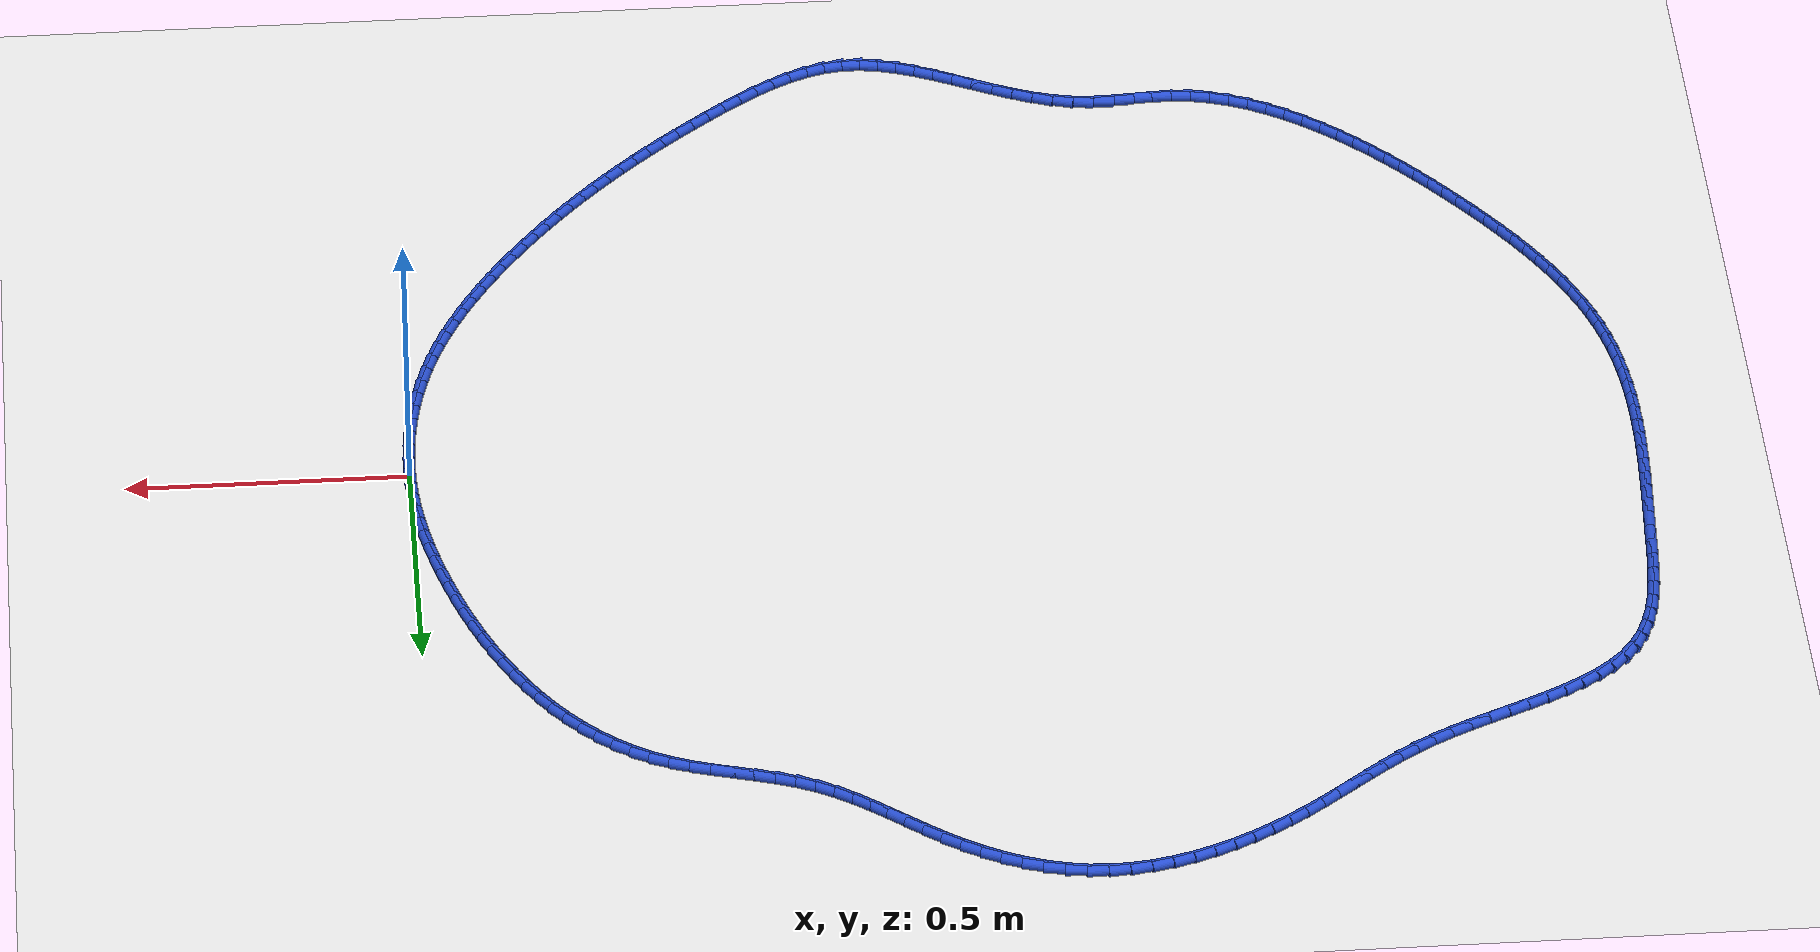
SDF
<sdf version="1.6">
 <world name="default">
  <light name="sun" type="directional">
   <pose>0 0 10 0 -0 0</pose>
   <diffuse>0.8 0.8 0.8 1</diffuse>
   <specular>0.2 0.2 0.2 1</specular>
   <attenuation>
    <range>1000</range>
    <constant>0.9</constant>
    <linear>0.01</linear>
    <quadratic>0.001</quadratic>
   </attenuation>
   <direction>-0.5 0.1 -0.9</direction>
  </light>
  <model name="ground_plane">
   <static>1</static>
   <link name="link">
    <collision name="collision">
     <geometry><plane><normal>0 0 1</normal><size>100 100</size></plane></geometry>
     <surface><friction><ode><mu>100</mu><mu2>50</mu2></ode></friction></surface>
    </collision>
    <visual name="visual">
     <cast_shadows>0</cast_shadows>
     <geometry><plane><normal>0 0 1</normal><size>100 100</size></plane></geometry>
     <material>
      <script><uri>file://media/materials/scripts/gazebo.material</uri><name>Gazebo/WhiteGlow</name></script>
     </material>
    </visual>
   </link>
  </model>
  <gravity>0 0 -9.8</gravity>
  <magnetic_field>6e-06 2.3e-05 -4.2e-05</magnetic_field>
  <atmosphere type="adiabatic"/>
  <physics name="default_physics" default="0" type="ode">
   <max_step_size>0.001</max_step_size>
   <real_time_factor>1</real_time_factor>
   <real_time_update_rate>1000</real_time_update_rate>
  </physics>
  <scene><ambient>0.4 0.4 0.4 1</ambient><background>0.7 0.7 0.7 1</background><shadows>1</shadows></scene>
  <spherical_coordinates>
   <surface_model>EARTH_WGS84</surface_model>
   <latitude_deg>0</latitude_deg>
   <longitude_deg>0</longitude_deg>
   <elevation>0</elevation>
   <heading_deg>0</heading_deg>
  </spherical_coordinates>
  <model name="line">
   <link name="link_0">
    <pose>-2.0816681711721685e-17 5.551115123125783e-17 0.01 0 1.57 -1.5418644426785577</pose>
    <collision name="collision">
     <geometry><cylinder><radius>0.01</radius><length>0.08</length></cylinder></geometry>
    </collision>
    <visual name="visual">
     <material>
      <script><name>Gazebo/Blue</name><uri>file://media/materials/scripts/gazebo.material</uri></script>
     </material>
     <geometry><cylinder><radius>0.01</radius><length>0.08</length></cylinder></geometry>
    </visual>
   </link>
   <link name="link_1">
    <pose>-0.001043050151081863 0.03604186650645524 0.01 0 1.57 -1.5042972054426107</pose>
    <collision name="collision">
     <geometry><cylinder><radius>0.01</radius><length>0.08</length></cylinder></geometry>
    </collision>
    <visual name="visual">
     <material>
      <script><name>Gazebo/Blue</name><uri>file://media/materials/scripts/gazebo.material</uri></script>
     </material>
     <geometry><cylinder><radius>0.01</radius><length>0.08</length></cylinder></geometry>
    </visual>
   </link>
   <link name="link_2">
    <pose>-0.0034332655557533552 0.0719324321773923 0.01 0 1.57 -1.46811828570782</pose>
    <collision name="collision">
     <geometry><cylinder><radius>0.01</radius><length>0.08</length></cylinder></geometry>
    </collision>
    <visual name="visual">
     <material>
      <script><name>Gazebo/Blue</name><uri>file://media/materials/scripts/gazebo.material</uri></script>
     </material>
     <geometry><cylinder><radius>0.01</radius><length>0.08</length></cylinder></geometry>
    </visual>
   </link>
   <link name="link_3">
    <pose>-0.007121036012133818 0.10772198868972027 0.01 0 1.57 -1.4335593581110762</pose>
    <collision name="collision">
     <geometry><cylinder><radius>0.01</radius><length>0.08</length></cylinder></geometry>
    </collision>
    <visual name="visual">
     <material>
      <script><name>Gazebo/Blue</name><uri>file://media/materials/scripts/gazebo.material</uri></script>
     </material>
     <geometry><cylinder><radius>0.01</radius><length>0.08</length></cylinder></geometry>
    </visual>
   </link>
   <link name="link_4">
    <pose>-0.012056751318342569 0.14346082772034818 0.01 0 1.57 -1.4008151488635772</pose>
    <collision name="collision">
     <geometry><cylinder><radius>0.01</radius><length>0.08</length></cylinder></geometry>
    </collision>
    <visual name="visual">
     <material>
      <script><name>Gazebo/Blue</name><uri>file://media/materials/scripts/gazebo.material</uri></script>
     </material>
     <geometry><cylinder><radius>0.01</radius><length>0.08</length></cylinder></geometry>
    </visual>
   </link>
   <link name="link_5">
    <pose>-0.018190801272498933 0.1791992409461852 0.01 0 1.57 -1.3700414256188014</pose>
    <collision name="collision">
     <geometry><cylinder><radius>0.01</radius><length>0.08</length></cylinder></geometry>
    </collision>
    <visual name="visual">
     <material>
      <script><name>Gazebo/Blue</name><uri>file://media/materials/scripts/gazebo.material</uri></script>
     </material>
     <geometry><cylinder><radius>0.01</radius><length>0.08</length></cylinder></geometry>
    </visual>
   </link>
   <link name="link_6">
    <pose>-0.025473575672722223 0.21498752004414012 0.01 0 1.57 -1.3413551120137432</pose>
    <collision name="collision">
     <geometry><cylinder><radius>0.01</radius><length>0.08</length></cylinder></geometry>
    </collision>
    <visual name="visual">
     <material>
      <script><name>Gazebo/Blue</name><uri>file://media/materials/scripts/gazebo.material</uri></script>
     </material>
     <geometry><cylinder><radius>0.01</radius><length>0.08</length></cylinder></geometry>
    </visual>
   </link>
   <link name="link_7">
    <pose>-0.03385546431713176 0.2508759566911221 0.01 0 1.57 -1.3148361497827756</pose>
    <collision name="collision">
     <geometry><cylinder><radius>0.01</radius><length>0.08</length></cylinder></geometry>
    </collision>
    <visual name="visual">
     <material>
      <script><name>Gazebo/Blue</name><uri>file://media/materials/scripts/gazebo.material</uri></script>
     </material>
     <geometry><cylinder><radius>0.01</radius><length>0.08</length></cylinder></geometry>
    </visual>
   </link>
   <link name="link_8">
    <pose>-0.043286857003846865 0.2869148425640402 0.01 0 1.57 -1.2905306463695272</pose>
    <collision name="collision">
     <geometry><cylinder><radius>0.01</radius><length>0.08</length></cylinder></geometry>
    </collision>
    <visual name="visual">
     <material>
      <script><name>Gazebo/Blue</name><uri>file://media/materials/scripts/gazebo.material</uri></script>
     </material>
     <geometry><cylinder><radius>0.01</radius><length>0.08</length></cylinder></geometry>
    </visual>
   </link>
   <link name="link_9">
    <pose>-0.05371814353098687 0.3231544693398034 0.01 0 1.57 -1.2678592212574724</pose>
    <collision name="collision">
     <geometry><cylinder><radius>0.01</radius><length>0.08</length></cylinder></geometry>
    </collision>
    <visual name="visual">
     <material>
      <script><name>Gazebo/Blue</name><uri>file://media/materials/scripts/gazebo.material</uri></script>
     </material>
     <geometry><cylinder><radius>0.01</radius><length>0.08</length></cylinder></geometry>
    </visual>
   </link>
   <link name="link_10">
    <pose>-0.06511291075346361 0.35961103518124893 0.01 0 1.57 -1.2440398850291174</pose>
    <collision name="collision">
     <geometry><cylinder><radius>0.01</radius><length>0.08</length></cylinder></geometry>
    </collision>
    <visual name="visual">
     <material>
      <script><name>Gazebo/Blue</name><uri>file://media/materials/scripts/gazebo.material</uri></script>
     </material>
     <geometry><cylinder><radius>0.01</radius><length>0.08</length></cylinder></geometry>
    </visual>
   </link>
   <link name="link_11">
    <pose>-0.07749471821590811 0.39614580372505437 0.01 0 1.57 -1.2181016882038407</pose>
    <collision name="collision">
     <geometry><cylinder><radius>0.01</radius><length>0.08</length></cylinder></geometry>
    </collision>
    <visual name="visual">
     <material>
      <script><name>Gazebo/Blue</name><uri>file://media/materials/scripts/gazebo.material</uri></script>
     </material>
     <geometry><cylinder><radius>0.01</radius><length>0.08</length></cylinder></geometry>
    </visual>
   </link>
   <link name="link_12">
    <pose>-0.09090415266593876 0.43257605022520107 0.01 0 1.57 -1.1898022638748929</pose>
    <collision name="collision">
     <geometry><cylinder><radius>0.01</radius><length>0.08</length></cylinder></geometry>
    </collision>
    <visual name="visual">
     <material>
      <script><name>Gazebo/Blue</name><uri>file://media/materials/scripts/gazebo.material</uri></script>
     </material>
     <geometry><cylinder><radius>0.01</radius><length>0.08</length></cylinder></geometry>
    </visual>
   </link>
   <link name="link_13">
    <pose>-0.10538180200431992 0.46871904695661176 0.01 0 1.57 -1.158868181699723</pose>
    <collision name="collision">
     <geometry><cylinder><radius>0.01</radius><length>0.08</length></cylinder></geometry>
    </collision>
    <visual name="visual">
     <material>
      <script><name>Gazebo/Blue</name><uri>file://media/materials/scripts/gazebo.material</uri></script>
     </material>
     <geometry><cylinder><radius>0.01</radius><length>0.08</length></cylinder></geometry>
    </visual>
   </link>
   <link name="link_14">
    <pose>-0.12096825413181589 0.5043920661942101 0.01 0 1.57 -1.1249930020174996</pose>
    <collision name="collision">
     <geometry><cylinder><radius>0.01</radius><length>0.08</length></cylinder></geometry>
    </collision>
    <visual name="visual">
     <material>
      <script><name>Gazebo/Blue</name><uri>file://media/materials/scripts/gazebo.material</uri></script>
     </material>
     <geometry><cylinder><radius>0.01</radius><length>0.08</length></cylinder></geometry>
    </visual>
   </link>
   <link name="link_15">
    <pose>-0.13770409694919122 0.5394123802129192 0.01 0 1.57 -1.0878365530715979</pose>
    <collision name="collision">
     <geometry><cylinder><radius>0.01</radius><length>0.08</length></cylinder></geometry>
    </collision>
    <visual name="visual">
     <material>
      <script><name>Gazebo/Blue</name><uri>file://media/materials/scripts/gazebo.material</uri></script>
     </material>
     <geometry><cylinder><radius>0.01</radius><length>0.08</length></cylinder></geometry>
    </visual>
   </link>
   <link name="link_16">
    <pose>-0.15562991835721016 0.5735972612876621 0.01 0 1.57 -1.047026320903879</pose>
    <collision name="collision">
     <geometry><cylinder><radius>0.01</radius><length>0.08</length></cylinder></geometry>
    </collision>
    <visual name="visual">
     <material>
      <script><name>Gazebo/Blue</name><uri>file://media/materials/scripts/gazebo.material</uri></script>
     </material>
     <geometry><cylinder><radius>0.01</radius><length>0.08</length></cylinder></geometry>
    </visual>
   </link>
   <link name="link_17">
    <pose>-0.1747863062566371 0.606763981693362 0.01 0 1.57 -1.002162322161715</pose>
    <collision name="collision">
     <geometry><cylinder><radius>0.01</radius><length>0.08</length></cylinder></geometry>
    </collision>
    <visual name="visual">
     <material>
      <script><name>Gazebo/Blue</name><uri>file://media/materials/scripts/gazebo.material</uri></script>
     </material>
     <geometry><cylinder><radius>0.01</radius><length>0.08</length></cylinder></geometry>
    </visual>
   </link>
   <link name="link_18">
    <pose>-0.19521384854823648 0.6387298137049426 0.01 0 1.57 -0.9528273553679396</pose>
    <collision name="collision">
     <geometry><cylinder><radius>0.01</radius><length>0.08</length></cylinder></geometry>
    </collision>
    <visual name="visual">
     <material>
      <script><name>Gazebo/Blue</name><uri>file://media/materials/scripts/gazebo.material</uri></script>
     </material>
     <geometry><cylinder><radius>0.01</radius><length>0.08</length></cylinder></geometry>
    </visual>
   </link>
   <link name="link_19">
    <pose>-0.21695313313277248 0.6693120295973263 0.01 0 1.57 -0.8986050735529741</pose>
    <collision name="collision">
     <geometry><cylinder><radius>0.01</radius><length>0.08</length></cylinder></geometry>
    </collision>
    <visual name="visual">
     <material>
      <script><name>Gazebo/Blue</name><uri>file://media/materials/scripts/gazebo.material</uri></script>
     </material>
     <geometry><cylinder><radius>0.01</radius><length>0.08</length></cylinder></geometry>
    </visual>
   </link>
   <link name="link_20">
    <pose>-0.24004474791100983 0.6983279016454369 0.01 0 1.57 -0.8391086953418703</pose>
    <collision name="collision">
     <geometry><cylinder><radius>0.01</radius><length>0.08</length></cylinder></geometry>
    </collision>
    <visual name="visual">
     <material>
      <script><name>Gazebo/Blue</name><uri>file://media/materials/scripts/gazebo.material</uri></script>
     </material>
     <geometry><cylinder><radius>0.01</radius><length>0.08</length></cylinder></geometry>
    </visual>
   </link>
   <link name="link_21">
    <pose>-0.2645292807837126 0.7255947021241973 0.01 0 1.57 -0.7740229837894332</pose>
    <collision name="collision">
     <geometry><cylinder><radius>0.01</radius><length>0.08</length></cylinder></geometry>
    </collision>
    <visual name="visual">
     <material>
      <script><name>Gazebo/Blue</name><uri>file://media/materials/scripts/gazebo.material</uri></script>
     </material>
     <geometry><cylinder><radius>0.01</radius><length>0.08</length></cylinder></geometry>
    </visual>
   </link>
   <link name="link_22">
    <pose>-0.2904473196516452 0.7509297033085308 0.01 0 1.57 -0.7031607464787559</pose>
    <collision name="collision">
     <geometry><cylinder><radius>0.01</radius><length>0.08</length></cylinder></geometry>
    </collision>
    <visual name="visual">
     <material>
      <script><name>Gazebo/Blue</name><uri>file://media/materials/scripts/gazebo.material</uri></script>
     </material>
     <geometry><cylinder><radius>0.01</radius><length>0.08</length></cylinder></geometry>
    </visual>
   </link>
   <link name="link_23">
    <pose>-0.3178394524155721 0.7741501774733606 0.01 0 1.57 -0.6265317830288788</pose>
    <collision name="collision">
     <geometry><cylinder><radius>0.01</radius><length>0.08</length></cylinder></geometry>
    </collision>
    <visual name="visual">
     <material>
      <script><name>Gazebo/Blue</name><uri>file://media/materials/scripts/gazebo.material</uri></script>
     </material>
     <geometry><cylinder><radius>0.01</radius><length>0.08</length></cylinder></geometry>
    </visual>
   </link>
   <link name="link_24">
    <pose>-0.34674626697625766 0.7950733968936099 0.01 0 1.57 -0.5444164518723954</pose>
    <collision name="collision">
     <geometry><cylinder><radius>0.01</radius><length>0.08</length></cylinder></geometry>
    </collision>
    <visual name="visual">
     <material>
      <script><name>Gazebo/Blue</name><uri>file://media/materials/scripts/gazebo.material</uri></script>
     </material>
     <geometry><cylinder><radius>0.01</radius><length>0.08</length></cylinder></geometry>
    </visual>
   </link>
   <link name="link_25">
    <pose>-0.3772083512344663 0.8135166338442017 0.01 0 1.57 -0.4574295171958053</pose>
    <collision name="collision">
     <geometry><cylinder><radius>0.01</radius><length>0.08</length></cylinder></geometry>
    </collision>
    <visual name="visual">
     <material>
      <script><name>Gazebo/Blue</name><uri>file://media/materials/scripts/gazebo.material</uri></script>
     </material>
     <geometry><cylinder><radius>0.01</radius><length>0.08</length></cylinder></geometry>
    </visual>
   </link>
   <link name="link_26">
    <pose>-0.40926627706350077 0.829297191951808 0.01 0 1.57 -0.37290345323113205</pose>
    <collision name="collision">
     <geometry><cylinder><radius>0.01</radius><length>0.08</length></cylinder></geometry>
    </collision>
    <visual name="visual">
     <material>
      <script><name>Gazebo/Blue</name><uri>file://media/materials/scripts/gazebo.material</uri></script>
     </material>
     <geometry><cylinder><radius>0.01</radius><length>0.08</length></cylinder></geometry>
    </visual>
   </link>
   <link name="link_27">
    <pose>-0.44285569538029007 0.8424376135469961 0.01 0 1.57 -0.3126170929630039</pose>
    <collision name="collision">
     <geometry><cylinder><radius>0.01</radius><length>0.08</length></cylinder></geometry>
    </collision>
    <visual name="visual">
     <material>
      <script><name>Gazebo/Blue</name><uri>file://media/materials/scripts/gazebo.material</uri></script>
     </material>
     <geometry><cylinder><radius>0.01</radius><length>0.08</length></cylinder></geometry>
    </visual>
   </link>
   <link name="link_28">
    <pose>-0.47755776934733923 0.85365386398829 0.01 0 1.57 -0.2799374048862171</pose>
    <collision name="collision">
     <geometry><cylinder><radius>0.01</radius><length>0.08</length></cylinder></geometry>
    </collision>
    <visual name="visual">
     <material>
      <script><name>Gazebo/Blue</name><uri>file://media/materials/scripts/gazebo.material</uri></script>
     </material>
     <geometry><cylinder><radius>0.01</radius><length>0.08</length></cylinder></geometry>
    </visual>
   </link>
   <link name="link_29">
    <pose>-0.5128788726544584 0.863808206332706 0.01 0 1.57 -0.2737848620738834</pose>
    <collision name="collision">
     <geometry><cylinder><radius>0.01</radius><length>0.08</length></cylinder></geometry>
    </collision>
    <visual name="visual">
     <material>
      <script><name>Gazebo/Blue</name><uri>file://media/materials/scripts/gazebo.material</uri></script>
     </material>
     <geometry><cylinder><radius>0.01</radius><length>0.08</length></cylinder></geometry>
    </visual>
   </link>
   <link name="link_30">
    <pose>-0.5483253789914568 0.8737629036372597 0.01 0 1.57 -0.2939090079821581</pose>
    <collision name="collision">
     <geometry><cylinder><radius>0.01</radius><length>0.08</length></cylinder></geometry>
    </collision>
    <visual name="visual">
     <material>
      <script><name>Gazebo/Blue</name><uri>file://media/materials/scripts/gazebo.material</uri></script>
     </material>
     <geometry><cylinder><radius>0.01</radius><length>0.08</length></cylinder></geometry>
    </visual>
   </link>
   <link name="link_31">
    <pose>-0.5834036620481452 0.884380218958967 0.01 0 1.57 -0.3410018294471774</pose>
    <collision name="collision">
     <geometry><cylinder><radius>0.01</radius><length>0.08</length></cylinder></geometry>
    </collision>
    <visual name="visual">
     <material>
      <script><name>Gazebo/Blue</name><uri>file://media/materials/scripts/gazebo.material</uri></script>
     </material>
     <geometry><cylinder><radius>0.01</radius><length>0.08</length></cylinder></geometry>
    </visual>
   </link>
   <link name="link_32">
    <pose>-0.6176200955143327 0.8965224153548433 0.01 0 1.57 -0.4162373211990734</pose>
    <collision name="collision">
     <geometry><cylinder><radius>0.01</radius><length>0.08</length></cylinder></geometry>
    </collision>
    <visual name="visual">
     <material>
      <script><name>Gazebo/Blue</name><uri>file://media/materials/scripts/gazebo.material</uri></script>
     </material>
     <geometry><cylinder><radius>0.01</radius><length>0.08</length></cylinder></geometry>
    </visual>
   </link>
   <link name="link_33">
    <pose>-0.6504822890800623 0.9110497078930023 0.01 0 1.57 -0.5067972024959382</pose>
    <collision name="collision">
     <geometry><cylinder><radius>0.01</radius><length>0.08</length></cylinder></geometry>
    </collision>
    <visual name="visual">
     <material>
      <script><name>Gazebo/Blue</name><uri>file://media/materials/scripts/gazebo.material</uri></script>
     </material>
     <geometry><cylinder><radius>0.01</radius><length>0.08</length></cylinder></geometry>
    </visual>
   </link>
   <link name="link_34">
    <pose>-0.6817482751100935 0.9284073741318992 0.01 0 1.57 -0.5817306728456535</pose>
    <collision name="collision">
     <geometry><cylinder><radius>0.01</radius><length>0.08</length></cylinder></geometry>
    </collision>
    <visual name="visual">
     <material>
      <script><name>Gazebo/Blue</name><uri>file://media/materials/scripts/gazebo.material</uri></script>
     </material>
     <geometry><cylinder><radius>0.01</radius><length>0.08</length></cylinder></geometry>
    </visual>
   </link>
   <link name="link_35">
    <pose>-0.7117292156095959 0.9481241842259708 0.01 0 1.57 -0.6362292502062338</pose>
    <collision name="collision">
     <geometry><cylinder><radius>0.01</radius><length>0.08</length></cylinder></geometry>
    </collision>
    <visual name="visual">
     <material>
      <script><name>Gazebo/Blue</name><uri>file://media/materials/scripts/gazebo.material</uri></script>
     </material>
     <geometry><cylinder><radius>0.01</radius><length>0.08</length></cylinder></geometry>
    </visual>
   </link>
   <link name="link_36">
    <pose>-0.7408102549185683 0.9696063234007654 0.01 0 1.57 -0.6704707630069232</pose>
    <collision name="collision">
     <geometry><cylinder><radius>0.01</radius><length>0.08</length></cylinder></geometry>
    </collision>
    <visual name="visual">
     <material>
      <script><name>Gazebo/Blue</name><uri>file://media/materials/scripts/gazebo.material</uri></script>
     </material>
     <geometry><cylinder><radius>0.01</radius><length>0.08</length></cylinder></geometry>
    </visual>
   </link>
   <link name="link_37">
    <pose>-0.7693765373770087 0.9922599768818308 0.01 0 1.57 -0.6849915208966761</pose>
    <collision name="collision">
     <geometry><cylinder><radius>0.01</radius><length>0.08</length></cylinder></geometry>
    </collision>
    <visual name="visual">
     <material>
      <script><name>Gazebo/Blue</name><uri>file://media/materials/scripts/gazebo.material</uri></script>
     </material>
     <geometry><cylinder><radius>0.01</radius><length>0.08</length></cylinder></geometry>
    </visual>
   </link>
   <link name="link_38">
    <pose>-0.7978132073249158 1.0154913298947157 0.01 0 1.57 -0.6802730916885902</pose>
    <collision name="collision">
     <geometry><cylinder><radius>0.01</radius><length>0.08</length></cylinder></geometry>
    </collision>
    <visual name="visual">
     <material>
      <script><name>Gazebo/Blue</name><uri>file://media/materials/scripts/gazebo.material</uri></script>
     </material>
     <geometry><cylinder><radius>0.01</radius><length>0.08</length></cylinder></geometry>
    </visual>
   </link>
   <link name="link_39">
    <pose>-0.8265054091022879 1.0387065676649678 0.01 0 1.57 -0.6565850541841763</pose>
    <collision name="collision">
     <geometry><cylinder><radius>0.01</radius><length>0.08</length></cylinder></geometry>
    </collision>
    <visual name="visual">
     <material>
      <script><name>Gazebo/Blue</name><uri>file://media/materials/scripts/gazebo.material</uri></script>
     </material>
     <geometry><cylinder><radius>0.01</radius><length>0.08</length></cylinder></geometry>
    </visual>
   </link>
   <link name="link_40">
    <pose>-0.8558382870491233 1.0613118754181352 0.01 0 1.57 -0.6140563984420399</pose>
    <collision name="collision">
     <geometry><cylinder><radius>0.01</radius><length>0.08</length></cylinder></geometry>
    </collision>
    <visual name="visual">
     <material>
      <script><name>Gazebo/Blue</name><uri>file://media/materials/scripts/gazebo.material</uri></script>
     </material>
     <geometry><cylinder><radius>0.01</radius><length>0.08</length></cylinder></geometry>
    </visual>
   </link>
   <link name="link_41">
    <pose>-0.8861965393699092 1.0827136528040269 0.01 0 1.57 -0.5565749575749159</pose>
    <collision name="collision">
     <geometry><cylinder><radius>0.01</radius><length>0.08</length></cylinder></geometry>
    </collision>
    <visual name="visual">
     <material>
      <script><name>Gazebo/Blue</name><uri>file://media/materials/scripts/gazebo.material</uri></script>
     </material>
     <geometry><cylinder><radius>0.01</radius><length>0.08</length></cylinder></geometry>
    </visual>
   </link>
   <link name="link_42">
    <pose>-0.9178186587334778 1.102388569632608 0.01 0 1.57 -0.49279196026768884</pose>
    <collision name="collision">
     <geometry><cylinder><radius>0.01</radius><length>0.08</length></cylinder></geometry>
    </collision>
    <visual name="visual">
     <material>
      <script><name>Gazebo/Blue</name><uri>file://media/materials/scripts/gazebo.material</uri></script>
     </material>
     <geometry><cylinder><radius>0.01</radius><length>0.08</length></cylinder></geometry>
    </visual>
   </link>
   <link name="link_43">
    <pose>-0.9505869589691657 1.1199844844720832 0.01 0 1.57 -0.4229951830318679</pose>
    <collision name="collision">
     <geometry><cylinder><radius>0.01</radius><length>0.08</length></cylinder></geometry>
    </collision>
    <visual name="visual">
     <material>
      <script><name>Gazebo/Blue</name><uri>file://media/materials/scripts/gazebo.material</uri></script>
     </material>
     <geometry><cylinder><radius>0.01</radius><length>0.08</length></cylinder></geometry>
    </visual>
   </link>
   <link name="link_44">
    <pose>-0.9843305441219974 1.1351748298885822 0.01 0 1.57 -0.34609199628701415</pose>
    <collision name="collision">
     <geometry><cylinder><radius>0.01</radius><length>0.08</length></cylinder></geometry>
    </collision>
    <visual name="visual">
     <material>
      <script><name>Gazebo/Blue</name><uri>file://media/materials/scripts/gazebo.material</uri></script>
     </material>
     <geometry><cylinder><radius>0.01</radius><length>0.08</length></cylinder></geometry>
    </visual>
   </link>
   <link name="link_45">
    <pose>-1.0188785182369968 1.1476330384482352 0.01 0 1.57 -0.26107415201446316</pose>
    <collision name="collision">
     <geometry><cylinder><radius>0.01</radius><length>0.08</length></cylinder></geometry>
    </collision>
    <visual name="visual">
     <material>
      <script><name>Gazebo/Blue</name><uri>file://media/materials/scripts/gazebo.material</uri></script>
     </material>
     <geometry><cylinder><radius>0.01</radius><length>0.08</length></cylinder></geometry>
    </visual>
   </link>
   <link name="link_46">
    <pose>-1.0540599853591888 1.1570325427171713 0.01 0 1.57 -0.1671558325617049</pose>
    <collision name="collision">
     <geometry><cylinder><radius>0.01</radius><length>0.08</length></cylinder></geometry>
    </collision>
    <visual name="visual">
     <material>
      <script><name>Gazebo/Blue</name><uri>file://media/materials/scripts/gazebo.material</uri></script>
     </material>
     <geometry><cylinder><radius>0.01</radius><length>0.08</length></cylinder></geometry>
    </visual>
   </link>
   <link name="link_47">
    <pose>-1.0897040495335966 1.1630467752615208 0.01 0 1.57 -0.06533915718364516</pose>
    <collision name="collision">
     <geometry><cylinder><radius>0.01</radius><length>0.08</length></cylinder></geometry>
    </collision>
    <visual name="visual">
     <material>
      <script><name>Gazebo/Blue</name><uri>file://media/materials/scripts/gazebo.material</uri></script>
     </material>
     <geometry><cylinder><radius>0.01</radius><length>0.08</length></cylinder></geometry>
    </visual>
   </link>
   <link name="link_48">
    <pose>-1.1256421204640559 1.1653982858403324 0.01 0 1.57 0.03356379665422837</pose>
    <collision name="collision">
     <geometry><cylinder><radius>0.01</radius><length>0.08</length></cylinder></geometry>
    </collision>
    <visual name="visual">
     <material>
      <script><name>Gazebo/Blue</name><uri>file://media/materials/scripts/gazebo.material</uri></script>
     </material>
     <geometry><cylinder><radius>0.01</radius><length>0.08</length></cylinder></geometry>
    </visual>
   </link>
   <link name="link_49">
    <pose>-1.1617233136616791 1.1641868090536158 0.01 0 1.57 0.12407549557857325</pose>
    <collision name="collision">
     <geometry><cylinder><radius>0.01</radius><length>0.08</length></cylinder></geometry>
    </collision>
    <visual name="visual">
     <material>
      <script><name>Gazebo/Blue</name><uri>file://media/materials/scripts/gazebo.material</uri></script>
     </material>
     <geometry><cylinder><radius>0.01</radius><length>0.08</length></cylinder></geometry>
    </visual>
   </link>
   <link name="link_50">
    <pose>-1.197804948557244 1.1596868466885155 0.01 0 1.57 0.2060781897681865</pose>
    <collision name="collision">
     <geometry><cylinder><radius>0.01</radius><length>0.08</length></cylinder></geometry>
    </collision>
    <visual name="visual">
     <material>
      <script><name>Gazebo/Blue</name><uri>file://media/materials/scripts/gazebo.material</uri></script>
     </material>
     <geometry><cylinder><radius>0.01</radius><length>0.08</length></cylinder></geometry>
    </visual>
   </link>
   <link name="link_51">
    <pose>-1.2337443893853823 1.1521738549837128 0.01 0 1.57 0.2799463031057654</pose>
    <collision name="collision">
     <geometry><cylinder><radius>0.01</radius><length>0.08</length></cylinder></geometry>
    </collision>
    <visual name="visual">
     <material>
      <script><name>Gazebo/Blue</name><uri>file://media/materials/scripts/gazebo.material</uri></script>
     </material>
     <geometry><cylinder><radius>0.01</radius><length>0.08</length></cylinder></geometry>
    </visual>
   </link>
   <link name="link_52">
    <pose>-1.2693990003807276 1.1419232901778882 0.01 0 1.57 0.3463321242342434</pose>
    <collision name="collision">
     <geometry><cylinder><radius>0.01</radius><length>0.08</length></cylinder></geometry>
    </collision>
    <visual name="visual">
     <material>
      <script><name>Gazebo/Blue</name><uri>file://media/materials/scripts/gazebo.material</uri></script>
     </material>
     <geometry><cylinder><radius>0.01</radius><length>0.08</length></cylinder></geometry>
    </visual>
   </link>
   <link name="link_53">
    <pose>-1.3046261457779105 1.1292106085097222 0.01 0 1.57 0.4060204560098023</pose>
    <collision name="collision">
     <geometry><cylinder><radius>0.01</radius><length>0.08</length></cylinder></geometry>
    </collision>
    <visual name="visual">
     <material>
      <script><name>Gazebo/Blue</name><uri>file://media/materials/scripts/gazebo.material</uri></script>
     </material>
     <geometry><cylinder><radius>0.01</radius><length>0.08</length></cylinder></geometry>
    </visual>
   </link>
   <link name="link_54">
    <pose>-1.3392831898115654 1.1143112662178951 0.01 0 1.57 0.45983160916772725</pose>
    <collision name="collision">
     <geometry><cylinder><radius>0.01</radius><length>0.08</length></cylinder></geometry>
    </collision>
    <visual name="visual">
     <material>
      <script><name>Gazebo/Blue</name><uri>file://media/materials/scripts/gazebo.material</uri></script>
     </material>
     <geometry><cylinder><radius>0.01</radius><length>0.08</length></cylinder></geometry>
    </visual>
   </link>
   <link name="link_55">
    <pose>-1.3732274967163227 1.0975007195410875 0.01 0 1.57 0.5085650074513908</pose>
    <collision name="collision">
     <geometry><cylinder><radius>0.01</radius><length>0.08</length></cylinder></geometry>
    </collision>
    <visual name="visual">
     <material>
      <script><name>Gazebo/Blue</name><uri>file://media/materials/scripts/gazebo.material</uri></script>
     </material>
     <geometry><cylinder><radius>0.01</radius><length>0.08</length></cylinder></geometry>
    </visual>
   </link>
   <link name="link_56">
    <pose>-1.4063164307268157 1.0790544247179805 0.01 0 1.57 0.5529721793952591</pose>
    <collision name="collision">
     <geometry><cylinder><radius>0.01</radius><length>0.08</length></cylinder></geometry>
    </collision>
    <visual name="visual">
     <material>
      <script><name>Gazebo/Blue</name><uri>file://media/materials/scripts/gazebo.material</uri></script>
     </material>
     <geometry><cylinder><radius>0.01</radius><length>0.08</length></cylinder></geometry>
    </visual>
   </link>
   <link name="link_57">
    <pose>-1.438407356077677 1.0592478379872543 0.01 0 1.57 0.5937478151766642</pose>
    <collision name="collision">
     <geometry><cylinder><radius>0.01</radius><length>0.08</length></cylinder></geometry>
    </collision>
    <visual name="visual">
     <material>
      <script><name>Gazebo/Blue</name><uri>file://media/materials/scripts/gazebo.material</uri></script>
     </material>
     <geometry><cylinder><radius>0.01</radius><length>0.08</length></cylinder></geometry>
    </visual>
   </link>
   <link name="link_58">
    <pose>-1.4693577332806766 1.0383564167907042 0.01 0 1.57 0.6296830662646028</pose>
    <collision name="collision">
     <geometry><cylinder><radius>0.01</radius><length>0.08</length></cylinder></geometry>
    </collision>
    <visual name="visual">
     <material>
      <script><name>Gazebo/Blue</name><uri>file://media/materials/scripts/gazebo.material</uri></script>
     </material>
     <geometry><cylinder><radius>0.01</radius><length>0.08</length></cylinder></geometry>
    </visual>
   </link>
   <link name="link_59">
    <pose>-1.4991388201825755 1.0166570406240547 0.01 0 1.57 0.6553149558138475</pose>
    <collision name="collision">
     <geometry><cylinder><radius>0.01</radius><length>0.08</length></cylinder></geometry>
    </collision>
    <visual name="visual">
     <material>
      <script><name>Gazebo/Blue</name><uri>file://media/materials/scripts/gazebo.material</uri></script>
     </material>
     <geometry><cylinder><radius>0.01</radius><length>0.08</length></cylinder></geometry>
    </visual>
   </link>
   <link name="link_60">
    <pose>-1.5280557544005724 0.9944307612691332 0.01 0 1.57 0.6690573040249587</pose>
    <collision name="collision">
     <geometry><cylinder><radius>0.01</radius><length>0.08</length></cylinder></geometry>
    </collision>
    <visual name="visual">
     <material>
      <script><name>Gazebo/Blue</name><uri>file://media/materials/scripts/gazebo.material</uri></script>
     </material>
     <geometry><cylinder><radius>0.01</radius><length>0.08</length></cylinder></geometry>
    </visual>
   </link>
   <link name="link_61">
    <pose>-1.5564745919502936 0.971959391766787 0.01 0 1.57 0.6705278611593852</pose>
    <collision name="collision">
     <geometry><cylinder><radius>0.01</radius><length>0.08</length></cylinder></geometry>
    </collision>
    <visual name="visual">
     <material>
      <script><name>Gazebo/Blue</name><uri>file://media/materials/scripts/gazebo.material</uri></script>
     </material>
     <geometry><cylinder><radius>0.01</radius><length>0.08</length></cylinder></geometry>
    </visual>
   </link>
   <link name="link_62">
    <pose>-1.5847613888473686 0.9495247451578651 0.01 0 1.57 0.6595834138137379</pose>
    <collision name="collision">
     <geometry><cylinder><radius>0.01</radius><length>0.08</length></cylinder></geometry>
    </collision>
    <visual name="visual">
     <material>
      <script><name>Gazebo/Blue</name><uri>file://media/materials/scripts/gazebo.material</uri></script>
     </material>
     <geometry><cylinder><radius>0.01</radius><length>0.08</length></cylinder></geometry>
    </visual>
   </link>
   <link name="link_63">
    <pose>-1.6132822011074246 0.9274086344832152 0.01 0 1.57 0.6363223212516911</pose>
    <collision name="collision">
     <geometry><cylinder><radius>0.01</radius><length>0.08</length></cylinder></geometry>
    </collision>
    <visual name="visual">
     <material>
      <script><name>Gazebo/Blue</name><uri>file://media/materials/scripts/gazebo.material</uri></script>
     </material>
     <geometry><cylinder><radius>0.01</radius><length>0.08</length></cylinder></geometry>
    </visual>
   </link>
   <link name="link_64">
    <pose>-1.6424030847460902 0.9058928727836851 0.01 0 1.57 0.6011304146199199</pose>
    <collision name="collision">
     <geometry><cylinder><radius>0.01</radius><length>0.08</length></cylinder></geometry>
    </collision>
    <visual name="visual">
     <material>
      <script><name>Gazebo/Blue</name><uri>file://media/materials/scripts/gazebo.material</uri></script>
     </material>
     <geometry><cylinder><radius>0.01</radius><length>0.08</length></cylinder></geometry>
    </visual>
   </link>
   <link name="link_65">
    <pose>-1.6724900957789928 0.8852592731001229 0.01 0 1.57 0.5547598329576889</pose>
    <collision name="collision">
     <geometry><cylinder><radius>0.01</radius><length>0.08</length></cylinder></geometry>
    </collision>
    <visual name="visual">
     <material>
      <script><name>Gazebo/Blue</name><uri>file://media/materials/scripts/gazebo.material</uri></script>
     </material>
     <geometry><cylinder><radius>0.01</radius><length>0.08</length></cylinder></geometry>
    </visual>
   </link>
   <link name="link_66">
    <pose>-1.703909278176348 0.8657896391444267 0.01 0 1.57 0.5032496964035219</pose>
    <collision name="collision">
     <geometry><cylinder><radius>0.01</radius><length>0.08</length></cylinder></geometry>
    </collision>
    <visual name="visual">
     <material>
      <script><name>Gazebo/Blue</name><uri>file://media/materials/scripts/gazebo.material</uri></script>
     </material>
     <geometry><cylinder><radius>0.01</radius><length>0.08</length></cylinder></geometry>
    </visual>
   </link>
   <link name="link_67">
    <pose>-1.736869513401699 0.8476440551586433 0.01 0 1.57 0.46383352152101903</pose>
    <collision name="collision">
     <geometry><cylinder><radius>0.01</radius><length>0.08</length></cylinder></geometry>
    </collision>
    <visual name="visual">
     <material>
      <script><name>Gazebo/Blue</name><uri>file://media/materials/scripts/gazebo.material</uri></script>
     </material>
     <geometry><cylinder><radius>0.01</radius><length>0.08</length></cylinder></geometry>
    </visual>
   </link>
   <link name="link_68">
    <pose>-1.7710292048929783 0.8305562702820016 0.01 0 1.57 0.43907663207008074</pose>
    <collision name="collision">
     <geometry><cylinder><radius>0.01</radius><length>0.08</length></cylinder></geometry>
    </collision>
    <visual name="visual">
     <material>
      <script><name>Gazebo/Blue</name><uri>file://media/materials/scripts/gazebo.material</uri></script>
     </material>
     <geometry><cylinder><radius>0.01</radius><length>0.08</length></cylinder></geometry>
    </visual>
   </link>
   <link name="link_69">
    <pose>-1.805926301827265 0.8141667440448871 0.01 0 1.57 0.4281187249552982</pose>
    <collision name="collision">
     <geometry><cylinder><radius>0.01</radius><length>0.08</length></cylinder></geometry>
    </collision>
    <visual name="visual">
     <material>
      <script><name>Gazebo/Blue</name><uri>file://media/materials/scripts/gazebo.material</uri></script>
     </material>
     <geometry><cylinder><radius>0.01</radius><length>0.08</length></cylinder></geometry>
    </visual>
   </link>
   <link name="link_70">
    <pose>-1.8410987533816388 0.7981159359776856 0.01 0 1.57 0.43062392808560934</pose>
    <collision name="collision">
     <geometry><cylinder><radius>0.01</radius><length>0.08</length></cylinder></geometry>
    </collision>
    <visual name="visual">
     <material>
      <script><name>Gazebo/Blue</name><uri>file://media/materials/scripts/gazebo.material</uri></script>
     </material>
     <geometry><cylinder><radius>0.01</radius><length>0.08</length></cylinder></geometry>
    </visual>
   </link>
   <link name="link_71">
    <pose>-1.8760845087331781 0.7820443056107813 0.01 0 1.57 0.44681507200156456</pose>
    <collision name="collision">
     <geometry><cylinder><radius>0.01</radius><length>0.08</length></cylinder></geometry>
    </collision>
    <visual name="visual">
     <material>
      <script><name>Gazebo/Blue</name><uri>file://media/materials/scripts/gazebo.material</uri></script>
     </material>
     <geometry><cylinder><radius>0.01</radius><length>0.08</length></cylinder></geometry>
    </visual>
   </link>
   <link name="link_72">
    <pose>-1.910421517058962 0.7655923124745602 0.01 0 1.57 0.4774860670784041</pose>
    <collision name="collision">
     <geometry><cylinder><radius>0.01</radius><length>0.08</length></cylinder></geometry>
    </collision>
    <visual name="visual">
     <material>
      <script><name>Gazebo/Blue</name><uri>file://media/materials/scripts/gazebo.material</uri></script>
     </material>
     <geometry><cylinder><radius>0.01</radius><length>0.08</length></cylinder></geometry>
    </visual>
   </link>
   <link name="link_73">
    <pose>-1.9436477275360695 0.7484004160994076 0.01 0 1.57 0.5239840310364703</pose>
    <collision name="collision">
     <geometry><cylinder><radius>0.01</radius><length>0.08</length></cylinder></geometry>
    </collision>
    <visual name="visual">
     <material>
      <script><name>Gazebo/Blue</name><uri>file://media/materials/scripts/gazebo.material</uri></script>
     </material>
     <geometry><cylinder><radius>0.01</radius><length>0.08</length></cylinder></geometry>
    </visual>
   </link>
   <link name="link_74">
    <pose>-1.9753010893415806 0.7301090760157085 0.01 0 1.57 0.5881120503958672</pose>
    <collision name="collision">
     <geometry><cylinder><radius>0.01</radius><length>0.08</length></cylinder></geometry>
    </collision>
    <visual name="visual">
     <material>
      <script><name>Gazebo/Blue</name><uri>file://media/materials/scripts/gazebo.material</uri></script>
     </material>
     <geometry><cylinder><radius>0.01</radius><length>0.08</length></cylinder></geometry>
    </visual>
   </link>
   <link name="link_75">
    <pose>-2.0049195516525726 0.7103587517538481 0.01 0 1.57 0.6718484188462909</pose>
    <collision name="collision">
     <geometry><cylinder><radius>0.01</radius><length>0.08</length></cylinder></geometry>
    </collision>
    <visual name="visual">
     <material>
      <script><name>Gazebo/Blue</name><uri>file://media/materials/scripts/gazebo.material</uri></script>
     </material>
     <geometry><cylinder><radius>0.01</radius><length>0.08</length></cylinder></geometry>
    </visual>
   </link>
   <link name="link_76">
    <pose>-2.0320410636461257 0.688789902844212 0.01 0 1.57 0.7767237448834062</pose>
    <collision name="collision">
     <geometry><cylinder><radius>0.01</radius><length>0.08</length></cylinder></geometry>
    </collision>
    <visual name="visual">
     <material>
      <script><name>Gazebo/Blue</name><uri>file://media/materials/scripts/gazebo.material</uri></script>
     </material>
     <geometry><cylinder><radius>0.01</radius><length>0.08</length></cylinder></geometry>
    </visual>
   </link>
   <link name="link_77">
    <pose>-2.0562035744993183 0.6650429888171852 0.01 0 1.57 0.9027290187404556</pose>
    <collision name="collision">
     <geometry><cylinder><radius>0.01</radius><length>0.08</length></cylinder></geometry>
    </collision>
    <visual name="visual">
     <material>
      <script><name>Gazebo/Blue</name><uri>file://media/materials/scripts/gazebo.material</uri></script>
     </material>
     <geometry><cylinder><radius>0.01</radius><length>0.08</length></cylinder></geometry>
    </visual>
   </link>
   <link name="link_78">
    <pose>-2.076945034959456 0.638758470437547 0.01 0 1.57 1.040788126843792</pose>
    <collision name="collision">
     <geometry><cylinder><radius>0.01</radius><length>0.08</length></cylinder></geometry>
    </collision>
    <visual name="visual">
     <material>
      <script><name>Gazebo/Blue</name><uri>file://media/materials/scripts/gazebo.material</uri></script>
     </material>
     <geometry><cylinder><radius>0.01</radius><length>0.08</length></cylinder></geometry>
    </visual>
   </link>
   <link name="link_79">
    <pose>-2.0939677054580987 0.6097059764523395 0.01 0 1.57 1.1634066429021501</pose>
    <collision name="collision">
     <geometry><cylinder><radius>0.01</radius><length>0.08</length></cylinder></geometry>
    </collision>
    <visual name="visual">
     <material>
      <script><name>Gazebo/Blue</name><uri>file://media/materials/scripts/gazebo.material</uri></script>
     </material>
     <geometry><cylinder><radius>0.01</radius><length>0.08</length></cylinder></geometry>
    </visual>
   </link>
   <link name="link_80">
    <pose>-2.107589719205668 0.5781392887158069 0.01 0 1.57 1.2639108332215279</pose>
    <collision name="collision">
     <geometry><cylinder><radius>0.01</radius><length>0.08</length></cylinder></geometry>
    </collision>
    <visual name="visual">
     <material>
      <script><name>Gazebo/Blue</name><uri>file://media/materials/scripts/gazebo.material</uri></script>
     </material>
     <geometry><cylinder><radius>0.01</radius><length>0.08</length></cylinder></geometry>
    </visual>
   </link>
   <link name="link_81">
    <pose>-2.118273479302894 0.5444256032775692 0.01 0 1.57 1.343539978818849</pose>
    <collision name="collision">
     <geometry><cylinder><radius>0.01</radius><length>0.08</length></cylinder></geometry>
    </collision>
    <visual name="visual">
     <material>
      <script><name>Gazebo/Blue</name><uri>file://media/materials/scripts/gazebo.material</uri></script>
     </material>
     <geometry><cylinder><radius>0.01</radius><length>0.08</length></cylinder></geometry>
    </visual>
   </link>
   <link name="link_82">
    <pose>-2.1264813888505074 0.5089321161872467 0.01 0 1.57 1.4045024636861867</pose>
    <collision name="collision">
     <geometry><cylinder><radius>0.01</radius><length>0.08</length></cylinder></geometry>
    </collision>
    <visual name="visual">
     <material>
      <script><name>Gazebo/Blue</name><uri>file://media/materials/scripts/gazebo.material</uri></script>
     </material>
     <geometry><cylinder><radius>0.01</radius><length>0.08</length></cylinder></geometry>
    </visual>
   </link>
   <link name="link_83">
    <pose>-2.132675850949237 0.47202602349446005 0.01 0 1.57 1.4490500726744204</pose>
    <collision name="collision">
     <geometry><cylinder><radius>0.01</radius><length>0.08</length></cylinder></geometry>
    </collision>
    <visual name="visual">
     <material>
      <script><name>Gazebo/Blue</name><uri>file://media/materials/scripts/gazebo.material</uri></script>
     </material>
     <geometry><cylinder><radius>0.01</radius><length>0.08</length></cylinder></geometry>
    </visual>
   </link>
   <link name="link_84">
    <pose>-2.1373192686998137 0.43407452124882884 0.01 0 1.57 1.4790329487114093</pose>
    <collision name="collision">
     <geometry><cylinder><radius>0.01</radius><length>0.08</length></cylinder></geometry>
    </collision>
    <visual name="visual">
     <material>
      <script><name>Gazebo/Blue</name><uri>file://media/materials/scripts/gazebo.material</uri></script>
     </material>
     <geometry><cylinder><radius>0.01</radius><length>0.08</length></cylinder></geometry>
    </visual>
   </link>
   <link name="link_85">
    <pose>-2.140874045202967 0.3954448054999738 0.01 0 1.57 1.4957326157029858</pose>
    <collision name="collision">
     <geometry><cylinder><radius>0.01</radius><length>0.08</length></cylinder></geometry>
    </collision>
    <visual name="visual">
     <material>
      <script><name>Gazebo/Blue</name><uri>file://media/materials/scripts/gazebo.material</uri></script>
     </material>
     <geometry><cylinder><radius>0.01</radius><length>0.08</length></cylinder></geometry>
    </visual>
   </link>
   <link name="link_86">
    <pose>-2.1438025835594265 0.3565040722975156 0.01 0 1.57 1.4999792832985925</pose>
    <collision name="collision">
     <geometry><cylinder><radius>0.01</radius><length>0.08</length></cylinder></geometry>
    </collision>
    <visual name="visual">
     <material>
      <script><name>Gazebo/Blue</name><uri>file://media/materials/scripts/gazebo.material</uri></script>
     </material>
     <geometry><cylinder><radius>0.01</radius><length>0.08</length></cylinder></geometry>
    </visual>
   </link>
   <link name="link_87">
    <pose>-2.1465611661075643 0.31761555916816414 0.01 0 1.57 1.4981795157230045</pose>
    <collision name="collision">
     <geometry><cylinder><radius>0.01</radius><length>0.08</length></cylinder></geometry>
    </collision>
    <visual name="visual">
     <material>
      <script><name>Gazebo/Blue</name><uri>file://media/materials/scripts/gazebo.material</uri></script>
     </material>
     <geometry><cylinder><radius>0.01</radius><length>0.08</length></cylinder></geometry>
    </visual>
   </link>
   <link name="link_88">
    <pose>-2.1493709401588452 0.2789904331388714 0.01 0 1.57 1.4984718022478933</pose>
    <collision name="collision">
     <geometry><cylinder><radius>0.01</radius><length>0.08</length></cylinder></geometry>
    </collision>
    <visual name="visual">
     <material>
      <script><name>Gazebo/Blue</name><uri>file://media/materials/scripts/gazebo.material</uri></script>
     </material>
     <geometry><cylinder><radius>0.01</radius><length>0.08</length></cylinder></geometry>
    </visual>
   </link>
   <link name="link_89">
    <pose>-2.1521492198441545 0.24064336110548437 0.01 0 1.57 1.5014530632102412</pose>
    <collision name="collision">
     <geometry><cylinder><radius>0.01</radius><length>0.08</length></cylinder></geometry>
    </collision>
    <visual name="visual">
     <material>
      <script><name>Gazebo/Blue</name><uri>file://media/materials/scripts/gazebo.material</uri></script>
     </material>
     <geometry><cylinder><radius>0.01</radius><length>0.08</length></cylinder></geometry>
    </visual>
   </link>
   <link name="link_90">
    <pose>-2.1547931753088387 0.20257598210497185 0.01 0 1.57 1.5071867514881798</pose>
    <collision name="collision">
     <geometry><cylinder><radius>0.01</radius><length>0.08</length></cylinder></geometry>
    </collision>
    <visual name="visual">
     <material>
      <script><name>Gazebo/Blue</name><uri>file://media/materials/scripts/gazebo.material</uri></script>
     </material>
     <geometry><cylinder><radius>0.01</radius><length>0.08</length></cylinder></geometry>
    </visual>
   </link>
   <link name="link_91">
    <pose>-2.1571999766982475 0.16478993517430177 0.01 0 1.57 1.5157414069779287</pose>
    <collision name="collision">
     <geometry><cylinder><radius>0.01</radius><length>0.08</length></cylinder></geometry>
    </collision>
    <visual name="visual">
     <material>
      <script><name>Gazebo/Blue</name><uri>file://media/materials/scripts/gazebo.material</uri></script>
     </material>
     <geometry><cylinder><radius>0.01</radius><length>0.08</length></cylinder></geometry>
    </visual>
   </link>
   <link name="link_92">
    <pose>-2.159266794157726 0.12728685935044298 0.01 0 1.57 1.5271896347010112</pose>
    <collision name="collision">
     <geometry><cylinder><radius>0.01</radius><length>0.08</length></cylinder></geometry>
    </collision>
    <visual name="visual">
     <material>
      <script><name>Gazebo/Blue</name><uri>file://media/materials/scripts/gazebo.material</uri></script>
     </material>
     <geometry><cylinder><radius>0.01</radius><length>0.08</length></cylinder></geometry>
    </visual>
   </link>
   <link name="link_93">
    <pose>-2.160890797832623 0.09006839367036445 0.01 0 1.57 1.541606263357041</pose>
    <collision name="collision">
     <geometry><cylinder><radius>0.01</radius><length>0.08</length></cylinder></geometry>
    </collision>
    <visual name="visual">
     <material>
      <script><name>Gazebo/Blue</name><uri>file://media/materials/scripts/gazebo.material</uri></script>
     </material>
     <geometry><cylinder><radius>0.01</radius><length>0.08</length></cylinder></geometry>
    </visual>
   </link>
   <link name="link_94">
    <pose>-2.1619691578682847 0.053136177171034 0.01 0 1.57 1.5590655394490902</pose>
    <collision name="collision">
     <geometry><cylinder><radius>0.01</radius><length>0.08</length></cylinder></geometry>
    </collision>
    <visual name="visual">
     <material>
      <script><name>Gazebo/Blue</name><uri>file://media/materials/scripts/gazebo.material</uri></script>
     </material>
     <geometry><cylinder><radius>0.01</radius><length>0.08</length></cylinder></geometry>
    </visual>
   </link>
   <link name="link_95">
    <pose>-2.1623990444100594 0.016491848889420634 0.01 0 1.57 -1.5619554468137218</pose>
    <collision name="collision">
     <geometry><cylinder><radius>0.01</radius><length>0.08</length></cylinder></geometry>
    </collision>
    <visual name="visual">
     <material>
      <script><name>Gazebo/Blue</name><uri>file://media/materials/scripts/gazebo.material</uri></script>
     </material>
     <geometry><cylinder><radius>0.01</radius><length>0.08</length></cylinder></geometry>
    </visual>
   </link>
   <link name="link_96">
    <pose>-2.162077627603294 -0.019862952137507116 0.01 0 1.57 -1.5382113161743758</pose>
    <collision name="collision">
     <geometry><cylinder><radius>0.01</radius><length>0.08</length></cylinder></geometry>
    </collision>
    <visual name="visual">
     <material>
      <script><name>Gazebo/Blue</name><uri>file://media/materials/scripts/gazebo.material</uri></script>
     </material>
     <geometry><cylinder><radius>0.01</radius><length>0.08</length></cylinder></geometry>
    </visual>
   </link>
   <link name="link_97">
    <pose>-2.1609020775933367 -0.0559265868727807 0.01 0 1.57 -1.5112508224448904</pose>
    <collision name="collision">
     <geometry><cylinder><radius>0.01</radius><length>0.08</length></cylinder></geometry>
    </collision>
    <visual name="visual">
     <material>
      <script><name>Gazebo/Blue</name><uri>file://media/materials/scripts/gazebo.material</uri></script>
     </material>
     <geometry><cylinder><radius>0.01</radius><length>0.08</length></cylinder></geometry>
    </visual>
   </link>
   <link name="link_98">
    <pose>-2.1587695645255334 -0.09169741627943076 0.01 0 1.57 -1.4810540534628895</pose>
    <collision name="collision">
     <geometry><cylinder><radius>0.01</radius><length>0.08</length></cylinder></geometry>
    </collision>
    <visual name="visual">
     <material>
      <script><name>Gazebo/Blue</name><uri>file://media/materials/scripts/gazebo.material</uri></script>
     </material>
     <geometry><cylinder><radius>0.01</radius><length>0.08</length></cylinder></geometry>
    </visual>
   </link>
   <link name="link_99">
    <pose>-2.1555772585452333 -0.12717380132049028 0.01 0 1.57 -1.4476340357738096</pose>
    <collision name="collision">
     <geometry><cylinder><radius>0.01</radius><length>0.08</length></cylinder></geometry>
    </collision>
    <visual name="visual">
     <material>
      <script><name>Gazebo/Blue</name><uri>file://media/materials/scripts/gazebo.material</uri></script>
     </material>
     <geometry><cylinder><radius>0.01</radius><length>0.08</length></cylinder></geometry>
    </visual>
   </link>
   <link name="link_100">
    <pose>-2.1512223297977826 -0.1623541029589899 0.01 0 1.57 -1.411046412082685</pose>
    <collision name="collision">
     <geometry><cylinder><radius>0.01</radius><length>0.08</length></cylinder></geometry>
    </collision>
    <visual name="visual">
     <material>
      <script><name>Gazebo/Blue</name><uri>file://media/materials/scripts/gazebo.material</uri></script>
     </material>
     <geometry><cylinder><radius>0.01</radius><length>0.08</length></cylinder></geometry>
    </visual>
   </link>
   <link name="link_101">
    <pose>-2.1456019484285296 -0.19723668215796106 0.01 0 1.57 -1.3713991465306667</pose>
    <collision name="collision">
     <geometry><cylinder><radius>0.01</radius><length>0.08</length></cylinder></geometry>
    </collision>
    <visual name="visual">
     <material>
      <script><name>Gazebo/Blue</name><uri>file://media/materials/scripts/gazebo.material</uri></script>
     </material>
     <geometry><cylinder><radius>0.01</radius><length>0.08</length></cylinder></geometry>
    </visual>
   </link>
   <link name="link_102">
    <pose>-2.1386132845828203 -0.23181989988043517 0.01 0 1.57 -1.3288612467266925</pose>
    <collision name="collision">
     <geometry><cylinder><radius>0.01</radius><length>0.08</length></cylinder></geometry>
    </collision>
    <visual name="visual">
     <material>
      <script><name>Gazebo/Blue</name><uri>file://media/materials/scripts/gazebo.material</uri></script>
     </material>
     <geometry><cylinder><radius>0.01</radius><length>0.08</length></cylinder></geometry>
    </visual>
   </link>
   <link name="link_103">
    <pose>-2.1301535084060026 -0.26610211708944365 0.01 0 1.57 -1.2836692231177191</pose>
    <collision name="collision">
     <geometry><cylinder><radius>0.01</radius><length>0.08</length></cylinder></geometry>
    </collision>
    <visual name="visual">
     <material>
      <script><name>Gazebo/Blue</name><uri>file://media/materials/scripts/gazebo.material</uri></script>
     </material>
     <geometry><cylinder><radius>0.01</radius><length>0.08</length></cylinder></geometry>
    </visual>
   </link>
   <link name="link_104">
    <pose>-2.120119790043425 -0.300081694748018 0.01 0 1.57 -1.2367530184318543</pose>
    <collision name="collision">
     <geometry><cylinder><radius>0.01</radius><length>0.08</length></cylinder></geometry>
    </collision>
    <visual name="visual">
     <material>
      <script><name>Gazebo/Blue</name><uri>file://media/materials/scripts/gazebo.material</uri></script>
     </material>
     <geometry><cylinder><radius>0.01</radius><length>0.08</length></cylinder></geometry>
    </visual>
   </link>
   <link name="link_105">
    <pose>-2.108433519906479 -0.3337549671649986 0.01 0 1.57 -1.1920728239836038</pose>
    <collision name="collision">
     <geometry><cylinder><radius>0.01</radius><length>0.08</length></cylinder></geometry>
    </collision>
    <visual name="visual">
     <material>
      <script><name>Gazebo/Blue</name><uri>file://media/materials/scripts/gazebo.material</uri></script>
     </material>
     <geometry><cylinder><radius>0.01</radius><length>0.08</length></cylinder></geometry>
    </visual>
   </link>
   <link name="link_106">
    <pose>-2.095162008775344 -0.36710605862121704 0.01 0 1.57 -1.1509383770899742</pose>
    <collision name="collision">
     <geometry><cylinder><radius>0.01</radius><length>0.08</length></cylinder></geometry>
    </collision>
    <visual name="visual">
     <material>
      <script><name>Gazebo/Blue</name><uri>file://media/materials/scripts/gazebo.material</uri></script>
     </material>
     <geometry><cylinder><radius>0.01</radius><length>0.08</length></cylinder></geometry>
    </visual>
   </link>
   <link name="link_107">
    <pose>-2.080426949484837 -0.4001145429264755 0.01 0 1.57 -1.1131927943329765</pose>
    <collision name="collision">
     <geometry><cylinder><radius>0.01</radius><length>0.08</length></cylinder></geometry>
    </collision>
    <visual name="visual">
     <material>
      <script><name>Gazebo/Blue</name><uri>file://media/materials/scripts/gazebo.material</uri></script>
     </material>
     <geometry><cylinder><radius>0.01</radius><length>0.08</length></cylinder></geometry>
    </visual>
   </link>
   <link name="link_108">
    <pose>-2.0643501271893756 -0.4327599861656451 0.01 0 1.57 -1.078659592820219</pose>
    <collision name="collision">
     <geometry><cylinder><radius>0.01</radius><length>0.08</length></cylinder></geometry>
    </collision>
    <visual name="visual">
     <material>
      <script><name>Gazebo/Blue</name><uri>file://media/materials/scripts/gazebo.material</uri></script>
     </material>
     <geometry><cylinder><radius>0.01</radius><length>0.08</length></cylinder></geometry>
    </visual>
   </link>
   <link name="link_109">
    <pose>-2.0470533270433795 -0.4650219544235969 0.01 0 1.57 -1.0471567376706261</pose>
    <collision name="collision">
     <geometry><cylinder><radius>0.01</radius><length>0.08</length></cylinder></geometry>
    </collision>
    <visual name="visual">
     <material>
      <script><name>Gazebo/Blue</name><uri>file://media/materials/scripts/gazebo.material</uri></script>
     </material>
     <geometry><cylinder><radius>0.01</radius><length>0.08</length></cylinder></geometry>
    </visual>
   </link>
   <link name="link_110">
    <pose>-2.028658334201267 -0.49688001378520164 0.01 0 1.57 -1.018505314304905</pose>
    <collision name="collision">
     <geometry><cylinder><radius>0.01</radius><length>0.08</length></cylinder></geometry>
    </collision>
    <visual name="visual">
     <material>
      <script><name>Gazebo/Blue</name><uri>file://media/materials/scripts/gazebo.material</uri></script>
     </material>
     <geometry><cylinder><radius>0.01</radius><length>0.08</length></cylinder></geometry>
    </visual>
   </link>
   <link name="link_111">
    <pose>-2.0092869338174584 -0.5283137303353306 0.01 0 1.57 -0.9925357504558703</pose>
    <collision name="collision">
     <geometry><cylinder><radius>0.01</radius><length>0.08</length></cylinder></geometry>
    </collision>
    <visual name="visual">
     <material>
      <script><name>Gazebo/Blue</name><uri>file://media/materials/scripts/gazebo.material</uri></script>
     </material>
     <geometry><cylinder><radius>0.01</radius><length>0.08</length></cylinder></geometry>
    </visual>
   </link>
   <link name="link_112">
    <pose>-1.9890609110463715 -0.5593026701588538 0.01 0 1.57 -0.9690921564413186</pose>
    <collision name="collision">
     <geometry><cylinder><radius>0.01</radius><length>0.08</length></cylinder></geometry>
    </collision>
    <visual name="visual">
     <material>
      <script><name>Gazebo/Blue</name><uri>file://media/materials/scripts/gazebo.material</uri></script>
     </material>
     <geometry><cylinder><radius>0.01</radius><length>0.08</length></cylinder></geometry>
    </visual>
   </link>
   <link name="link_113">
    <pose>-1.9681020510424252 -0.5898263993406438 0.01 0 1.57 -0.9480353060623581</pose>
    <collision name="collision">
     <geometry><cylinder><radius>0.01</radius><length>0.08</length></cylinder></geometry>
    </collision>
    <visual name="visual">
     <material>
      <script><name>Gazebo/Blue</name><uri>file://media/materials/scripts/gazebo.material</uri></script>
     </material>
     <geometry><cylinder><radius>0.01</radius><length>0.08</length></cylinder></geometry>
    </visual>
   </link>
   <link name="link_114">
    <pose>-1.946532138960039 -0.6198644839655709 0.01 0 1.57 -0.9292447086996409</pose>
    <collision name="collision">
     <geometry><cylinder><radius>0.01</radius><length>0.08</length></cylinder></geometry>
    </collision>
    <visual name="visual">
     <material>
      <script><name>Gazebo/Blue</name><uri>file://media/materials/scripts/gazebo.material</uri></script>
     </material>
     <geometry><cylinder><radius>0.01</radius><length>0.08</length></cylinder></geometry>
    </visual>
   </link>
   <link name="link_115">
    <pose>-1.924472959953631 -0.6493964901185058 0.01 0 1.57 -0.9126201500073163</pose>
    <collision name="collision">
     <geometry><cylinder><radius>0.01</radius><length>0.08</length></cylinder></geometry>
    </collision>
    <visual name="visual">
     <material>
      <script><name>Gazebo/Blue</name><uri>file://media/materials/scripts/gazebo.material</uri></script>
     </material>
     <geometry><cylinder><radius>0.01</radius><length>0.08</length></cylinder></geometry>
    </visual>
   </link>
   <link name="link_116">
    <pose>-1.9020462991776221 -0.67840198388432 0.01 0 1.57 -0.897500401250793</pose>
    <collision name="collision">
     <geometry><cylinder><radius>0.01</radius><length>0.08</length></cylinder></geometry>
    </collision>
    <visual name="visual">
     <material>
      <script><name>Gazebo/Blue</name><uri>file://media/materials/scripts/gazebo.material</uri></script>
     </material>
     <geometry><cylinder><radius>0.01</radius><length>0.08</length></cylinder></geometry>
    </visual>
   </link>
   <link name="link_117">
    <pose>-1.8793444217026667 -0.7068635446658009 0.01 0 1.57 -0.880170001372706</pose>
    <collision name="collision">
     <geometry><cylinder><radius>0.01</radius><length>0.08</length></cylinder></geometry>
    </collision>
    <visual name="visual">
     <material>
      <script><name>Gazebo/Blue</name><uri>file://media/materials/scripts/gazebo.material</uri></script>
     </material>
     <geometry><cylinder><radius>0.01</radius><length>0.08</length></cylinder></geometry>
    </visual>
   </link>
   <link name="link_118">
    <pose>-1.8562721701270268 -0.7347828833661295 0.01 0 1.57 -0.8592908617874514</pose>
    <collision name="collision">
     <geometry><cylinder><radius>0.01</radius><length>0.08</length></cylinder></geometry>
    </collision>
    <visual name="visual">
     <material>
      <script><name>Gazebo/Blue</name><uri>file://media/materials/scripts/gazebo.material</uri></script>
     </material>
     <geometry><cylinder><radius>0.01</radius><length>0.08</length></cylinder></geometry>
    </visual>
   </link>
   <link name="link_119">
    <pose>-1.832661068503717 -0.7621691950165079 0.01 0 1.57 -0.8350611824157842</pose>
    <collision name="collision">
     <geometry><cylinder><radius>0.01</radius><length>0.08</length></cylinder></geometry>
    </collision>
    <visual name="visual">
     <material>
      <script><name>Gazebo/Blue</name><uri>file://media/materials/scripts/gazebo.material</uri></script>
     </material>
     <geometry><cylinder><radius>0.01</radius><length>0.08</length></cylinder></geometry>
    </visual>
   </link>
   <link name="link_120">
    <pose>-1.8083424709797136 -0.7890316919916143 0.01 0 1.57 -0.8077672773597999</pose>
    <collision name="collision">
     <geometry><cylinder><radius>0.01</radius><length>0.08</length></cylinder></geometry>
    </collision>
    <visual name="visual">
     <material>
      <script><name>Gazebo/Blue</name><uri>file://media/materials/scripts/gazebo.material</uri></script>
     </material>
     <geometry><cylinder><radius>0.01</radius><length>0.08</length></cylinder></geometry>
    </visual>
   </link>
   <link name="link_121">
    <pose>-1.7831477317019935 -0.8153795866661271 0.01 0 1.57 -0.7777752955231665</pose>
    <collision name="collision">
     <geometry><cylinder><radius>0.01</radius><length>0.08</length></cylinder></geometry>
    </collision>
    <visual name="visual">
     <material>
      <script><name>Gazebo/Blue</name><uri>file://media/materials/scripts/gazebo.material</uri></script>
     </material>
     <geometry><cylinder><radius>0.01</radius><length>0.08</length></cylinder></geometry>
    </visual>
   </link>
   <link name="link_122">
    <pose>-1.7569082048175337 -0.8412220914147248 0.01 0 1.57 -0.7454205065900692</pose>
    <collision name="collision">
     <geometry><cylinder><radius>0.01</radius><length>0.08</length></cylinder></geometry>
    </collision>
    <visual name="visual">
     <material>
      <script><name>Gazebo/Blue</name><uri>file://media/materials/scripts/gazebo.material</uri></script>
     </material>
     <geometry><cylinder><radius>0.01</radius><length>0.08</length></cylinder></geometry>
    </visual>
   </link>
   <link name="link_123">
    <pose>-1.7294613422253124 -0.8665577092591208 0.01 0 1.57 -0.7089347568070417</pose>
    <collision name="collision">
     <geometry><cylinder><radius>0.01</radius><length>0.08</length></cylinder></geometry>
    </collision>
    <visual name="visual">
     <material>
      <script><name>Gazebo/Blue</name><uri>file://media/materials/scripts/gazebo.material</uri></script>
     </material>
     <geometry><cylinder><radius>0.01</radius><length>0.08</length></cylinder></geometry>
    </visual>
   </link>
   <link name="link_124">
    <pose>-1.7007689457497235 -0.8911665500751561 0.01 0 1.57 -0.6659031467843936</pose>
    <collision name="collision">
     <geometry><cylinder><radius>0.01</radius><length>0.08</length></cylinder></geometry>
    </collision>
    <visual name="visual">
     <material>
      <script><name>Gazebo/Blue</name><uri>file://media/materials/scripts/gazebo.material</uri></script>
     </material>
     <geometry><cylinder><radius>0.01</radius><length>0.08</length></cylinder></geometry>
    </visual>
   </link>
   <link name="link_125">
    <pose>-1.6709089278376925 -0.9146248011063067 0.01 0 1.57 -0.6153594984852437</pose>
    <collision name="collision">
     <geometry><cylinder><radius>0.01</radius><length>0.08</length></cylinder></geometry>
    </collision>
    <visual name="visual">
     <material>
      <script><name>Gazebo/Blue</name><uri>file://media/materials/scripts/gazebo.material</uri></script>
     </material>
     <geometry><cylinder><radius>0.01</radius><length>0.08</length></cylinder></geometry>
    </visual>
   </link>
   <link name="link_126">
    <pose>-1.6399636483993292 -0.9365008386104631 0.01 0 1.57 -0.5562231241861842</pose>
    <collision name="collision">
     <geometry><cylinder><radius>0.01</radius><length>0.08</length></cylinder></geometry>
    </collision>
    <visual name="visual">
     <material>
      <script><name>Gazebo/Blue</name><uri>file://media/materials/scripts/gazebo.material</uri></script>
     </material>
     <geometry><cylinder><radius>0.01</radius><length>0.08</length></cylinder></geometry>
    </visual>
   </link>
   <link name="link_127">
    <pose>-1.608015467344742 -0.9563630388455138 0.01 0 1.57 -0.4872710765406199</pose>
    <collision name="collision">
     <geometry><cylinder><radius>0.01</radius><length>0.08</length></cylinder></geometry>
    </collision>
    <visual name="visual">
     <material>
      <script><name>Gazebo/Blue</name><uri>file://media/materials/scripts/gazebo.material</uri></script>
     </material>
     <geometry><cylinder><radius>0.01</radius><length>0.08</length></cylinder></geometry>
    </visual>
   </link>
   <link name="link_128">
    <pose>-1.5751467445840384 -0.973779778069347 0.01 0 1.57 -0.40724136874940015</pose>
    <collision name="collision">
     <geometry><cylinder><radius>0.01</radius><length>0.08</length></cylinder></geometry>
    </collision>
    <visual name="visual">
     <material>
      <script><name>Gazebo/Blue</name><uri>file://media/materials/scripts/gazebo.material</uri></script>
     </material>
     <geometry><cylinder><radius>0.01</radius><length>0.08</length></cylinder></geometry>
    </visual>
   </link>
   <link name="link_129">
    <pose>-1.5414398400273286 -0.9883194325398523 0.01 0 1.57 -0.31503372649115174</pose>
    <collision name="collision">
     <geometry><cylinder><radius>0.01</radius><length>0.08</length></cylinder></geometry>
    </collision>
    <visual name="visual">
     <material>
      <script><name>Gazebo/Blue</name><uri>file://media/materials/scripts/gazebo.material</uri></script>
     </material>
     <geometry><cylinder><radius>0.01</radius><length>0.08</length></cylinder></geometry>
    </visual>
   </link>
   <link name="link_130">
    <pose>-1.50697711358472 -0.9995503785149179 0.01 0 1.57 -0.21004357559563314</pose>
    <collision name="collision">
     <geometry><cylinder><radius>0.01</radius><length>0.08</length></cylinder></geometry>
    </collision>
    <visual name="visual">
     <material>
      <script><name>Gazebo/Blue</name><uri>file://media/materials/scripts/gazebo.material</uri></script>
     </material>
     <geometry><cylinder><radius>0.01</radius><length>0.08</length></cylinder></geometry>
    </visual>
   </link>
   <link name="link_131">
    <pose>-1.4718409251663223 -1.0070409922524335 0.01 0 1.57 -0.09291246672937445</pose>
    <collision name="collision">
     <geometry><cylinder><radius>0.01</radius><length>0.08</length></cylinder></geometry>
    </collision>
    <visual name="visual">
     <material>
      <script><name>Gazebo/Blue</name><uri>file://media/materials/scripts/gazebo.material</uri></script>
     </material>
     <geometry><cylinder><radius>0.01</radius><length>0.08</length></cylinder></geometry>
    </visual>
   </link>
   <link name="link_132">
    <pose>-1.436114104183527 -1.010370044435054 0.01 0 1.57 0.01226644461522866</pose>
    <collision name="collision">
     <geometry><cylinder><radius>0.01</radius><length>0.08</length></cylinder></geometry>
    </collision>
    <visual name="visual">
     <material>
      <script><name>Gazebo/Blue</name><uri>file://media/materials/scripts/gazebo.material</uri></script>
     </material>
     <geometry><cylinder><radius>0.01</radius><length>0.08</length></cylinder></geometry>
    </visual>
   </link>
   <link name="link_133">
    <pose>-1.3999160528126446 -1.0099260007714024 0.01 0 1.57 0.06712923105164754</pose>
    <collision name="collision">
     <geometry><cylinder><radius>0.01</radius><length>0.08</length></cylinder></geometry>
    </collision>
    <visual name="visual">
     <material>
      <script><name>Gazebo/Blue</name><uri>file://media/materials/scripts/gazebo.material</uri></script>
     </material>
     <geometry><cylinder><radius>0.01</radius><length>0.08</length></cylinder></geometry>
    </visual>
   </link>
   <link name="link_134">
    <pose>-1.3634283068215303 -1.0074729205333897 0.01 0 1.57 0.0699710948933142</pose>
    <collision name="collision">
     <geometry><cylinder><radius>0.01</radius><length>0.08</length></cylinder></geometry>
    </collision>
    <visual name="visual">
     <material>
      <script><name>Gazebo/Blue</name><uri>file://media/materials/scripts/gazebo.material</uri></script>
     </material>
     <geometry><cylinder><radius>0.01</radius><length>0.08</length></cylinder></geometry>
    </visual>
   </link>
   <link name="link_135">
    <pose>-1.3268384382111456 -1.0049085009044632 0.01 0 1.57 0.021310955273371936</pose>
    <collision name="collision">
     <geometry><cylinder><radius>0.01</radius><length>0.08</length></cylinder></geometry>
    </collision>
    <visual name="visual">
     <material>
      <script><name>Gazebo/Blue</name><uri>file://media/materials/scripts/gazebo.material</uri></script>
     </material>
     <geometry><cylinder><radius>0.01</radius><length>0.08</length></cylinder></geometry>
    </visual>
   </link>
   <link name="link_136">
    <pose>-1.290334018982451 -1.0041304390680719 0.01 0 1.57 -0.07945518711868803</pose>
    <collision name="collision">
     <geometry><cylinder><radius>0.01</radius><length>0.08</length></cylinder></geometry>
    </collision>
    <visual name="visual">
     <material>
      <script><name>Gazebo/Blue</name><uri>file://media/materials/scripts/gazebo.material</uri></script>
     </material>
     <geometry><cylinder><radius>0.01</radius><length>0.08</length></cylinder></geometry>
    </visual>
   </link>
   <link name="link_137">
    <pose>-1.2541009896510025 -1.007015414822726 0.01 0 1.57 -0.20226732589746513</pose>
    <collision name="collision">
     <geometry><cylinder><radius>0.01</radius><length>0.08</length></cylinder></geometry>
    </collision>
    <visual name="visual">
     <material>
      <script><name>Gazebo/Blue</name><uri>file://media/materials/scripts/gazebo.material</uri></script>
     </material>
     <geometry><cylinder><radius>0.01</radius><length>0.08</length></cylinder></geometry>
    </visual>
   </link>
   <link name="link_138">
    <pose>-1.2182421489388675 -1.014369045320099 0.01 0 1.57 -0.3022175208335319</pose>
    <collision name="collision">
     <geometry><cylinder><radius>0.01</radius><length>0.08</length></cylinder></geometry>
    </collision>
    <visual name="visual">
     <material>
      <script><name>Gazebo/Blue</name><uri>file://media/materials/scripts/gazebo.material</uri></script>
     </material>
     <geometry><cylinder><radius>0.01</radius><length>0.08</length></cylinder></geometry>
    </visual>
   </link>
   <link name="link_139">
    <pose>-1.1827392579734501 -1.0254376976515822 0.01 0 1.57 -0.37650905169983717</pose>
    <collision name="collision">
     <geometry><cylinder><radius>0.01</radius><length>0.08</length></cylinder></geometry>
    </collision>
    <visual name="visual">
     <material>
      <script><name>Gazebo/Blue</name><uri>file://media/materials/scripts/gazebo.material</uri></script>
     </material>
     <geometry><cylinder><radius>0.01</radius><length>0.08</length></cylinder></geometry>
    </visual>
   </link>
   <link name="link_140">
    <pose>-1.1475645305348101 -1.0393447465278833 0.01 0 1.57 -0.42702767888800364</pose>
    <collision name="collision">
     <geometry><cylinder><radius>0.01</radius><length>0.08</length></cylinder></geometry>
    </collision>
    <visual name="visual">
     <material>
      <script><name>Gazebo/Blue</name><uri>file://media/materials/scripts/gazebo.material</uri></script>
     </material>
     <geometry><cylinder><radius>0.01</radius><length>0.08</length></cylinder></geometry>
    </visual>
   </link>
   <link name="link_141">
    <pose>-1.1126901804030085 -1.0552135666597084 0.01 0 1.57 -0.45559477577948687</pose>
    <collision name="collision">
     <geometry><cylinder><radius>0.01</radius><length>0.08</length></cylinder></geometry>
    </collision>
    <visual name="visual">
     <material>
      <script><name>Gazebo/Blue</name><uri>file://media/materials/scripts/gazebo.material</uri></script>
     </material>
     <geometry><cylinder><radius>0.01</radius><length>0.08</length></cylinder></geometry>
    </visual>
   </link>
   <link name="link_142">
    <pose>-1.0780884213581066 -1.0721675327577656 0.01 0 1.57 -0.46327520600898886</pose>
    <collision name="collision">
     <geometry><cylinder><radius>0.01</radius><length>0.08</length></cylinder></geometry>
    </collision>
    <visual name="visual">
     <material>
      <script><name>Gazebo/Blue</name><uri>file://media/materials/scripts/gazebo.material</uri></script>
     </material>
     <geometry><cylinder><radius>0.01</radius><length>0.08</length></cylinder></geometry>
    </visual>
   </link>
   <link name="link_143">
    <pose>-1.0437314671801652 -1.0893300195327604 0.01 0 1.57 -0.4500691885193759</pose>
    <collision name="collision">
     <geometry><cylinder><radius>0.01</radius><length>0.08</length></cylinder></geometry>
    </collision>
    <visual name="visual">
     <material>
      <script><name>Gazebo/Blue</name><uri>file://media/materials/scripts/gazebo.material</uri></script>
     </material>
     <geometry><cylinder><radius>0.01</radius><length>0.08</length></cylinder></geometry>
    </visual>
   </link>
   <link name="link_144">
    <pose>-1.0095915316492452 -1.1058244016954004 0.01 0 1.57 -0.4147867487717466</pose>
    <collision name="collision">
     <geometry><cylinder><radius>0.01</radius><length>0.08</length></cylinder></geometry>
    </collision>
    <visual name="visual">
     <material>
      <script><name>Gazebo/Blue</name><uri>file://media/materials/scripts/gazebo.material</uri></script>
     </material>
     <geometry><cylinder><radius>0.01</radius><length>0.08</length></cylinder></geometry>
    </visual>
   </link>
   <link name="link_145">
    <pose>-0.9756408285454082 -1.1207740539563924 0.01 0 1.57 -0.35506364588897443</pose>
    <collision name="collision">
     <geometry><cylinder><radius>0.01</radius><length>0.08</length></cylinder></geometry>
    </collision>
    <visual name="visual">
     <material>
      <script><name>Gazebo/Blue</name><uri>file://media/materials/scripts/gazebo.material</uri></script>
     </material>
     <geometry><cylinder><radius>0.01</radius><length>0.08</length></cylinder></geometry>
    </visual>
   </link>
   <link name="link_146">
    <pose>-0.9418515716487137 -1.1333023510264435 0.01 0 1.57 -0.26767624566615017</pose>
    <collision name="collision">
     <geometry><cylinder><radius>0.01</radius><length>0.08</length></cylinder></geometry>
    </collision>
    <visual name="visual">
     <material>
      <script><name>Gazebo/Blue</name><uri>file://media/materials/scripts/gazebo.material</uri></script>
     </material>
     <geometry><cylinder><radius>0.01</radius><length>0.08</length></cylinder></geometry>
    </visual>
   </link>
   <link name="link_147">
    <pose>-0.9081959747392231 -1.1425326676162602 0.01 0 1.57 -0.14956769890173596</pose>
    <collision name="collision">
     <geometry><cylinder><radius>0.01</radius><length>0.08</length></cylinder></geometry>
    </collision>
    <visual name="visual">
     <material>
      <script><name>Gazebo/Blue</name><uri>file://media/materials/scripts/gazebo.material</uri></script>
     </material>
     <geometry><cylinder><radius>0.01</radius><length>0.08</length></cylinder></geometry>
    </visual>
   </link>
   <link name="link_148">
    <pose>-0.8746462515969972 -1.1475883784365495 0.01 0 1.57 -0.00017499034555581747</pose>
    <collision name="collision">
     <geometry><cylinder><radius>0.01</radius><length>0.08</length></cylinder></geometry>
    </collision>
    <visual name="visual">
     <material>
      <script><name>Gazebo/Blue</name><uri>file://media/materials/scripts/gazebo.material</uri></script>
     </material>
     <geometry><cylinder><radius>0.01</radius><length>0.08</length></cylinder></geometry>
    </visual>
   </link>
   <link name="link_149">
    <pose>-0.8411747187085692 -1.1475942356317157 0.01 0 1.57 0.16299693353481376</pose>
    <collision name="collision">
     <geometry><cylinder><radius>0.01</radius><length>0.08</length></cylinder></geometry>
    </collision>
    <visual name="visual">
     <material>
      <script><name>Gazebo/Blue</name><uri>file://media/materials/scripts/gazebo.material</uri></script>
     </material>
     <geometry><cylinder><radius>0.01</radius><length>0.08</length></cylinder></geometry>
    </visual>
   </link>
   <link name="link_150">
    <pose>-0.8077856213712263 -1.1421032001922433 0.01 0 1.57 0.3034077067660393</pose>
    <collision name="collision">
     <geometry><cylinder><radius>0.01</radius><length>0.08</length></cylinder></geometry>
    </collision>
    <visual name="visual">
     <material>
      <script><name>Gazebo/Blue</name><uri>file://media/materials/scripts/gazebo.material</uri></script>
     </material>
     <geometry><cylinder><radius>0.01</radius><length>0.08</length></cylinder></geometry>
    </visual>
   </link>
   <link name="link_151">
    <pose>-0.7745602261416399 -1.1317011931163743 0.01 0 1.57 0.4162345979605556</pose>
    <collision name="collision">
     <geometry><cylinder><radius>0.01</radius><length>0.08</length></cylinder></geometry>
    </collision>
    <visual name="visual">
     <material>
      <script><name>Gazebo/Blue</name><uri>file://media/materials/scripts/gazebo.material</uri></script>
     </material>
     <geometry><cylinder><radius>0.01</radius><length>0.08</length></cylinder></geometry>
    </visual>
   </link>
   <link name="link_152">
    <pose>-0.741591180734068 -1.1171267722291456 0.01 0 1.57 0.5044246599722264</pose>
    <collision name="collision">
     <geometry><cylinder><radius>0.01</radius><length>0.08</length></cylinder></geometry>
    </collision>
    <visual name="visual">
     <material>
      <script><name>Gazebo/Blue</name><uri>file://media/materials/scripts/gazebo.material</uri></script>
     </material>
     <geometry><cylinder><radius>0.01</radius><length>0.08</length></cylinder></geometry>
    </visual>
   </link>
   <link name="link_153">
    <pose>-0.7089711328627667 -1.0991184953555937 0.01 0 1.57 0.5717212980597471</pose>
    <collision name="collision">
     <geometry><cylinder><radius>0.01</radius><length>0.08</length></cylinder></geometry>
    </collision>
    <visual name="visual">
     <material>
      <script><name>Gazebo/Blue</name><uri>file://media/materials/scripts/gazebo.material</uri></script>
     </material>
     <geometry><cylinder><radius>0.01</radius><length>0.08</length></cylinder></geometry>
    </visual>
   </link>
   <link name="link_154">
    <pose>-0.6767927302419945 -1.0784149203207554 0.01 0 1.57 0.6214491476171118</pose>
    <collision name="collision">
     <geometry><cylinder><radius>0.01</radius><length>0.08</length></cylinder></geometry>
    </collision>
    <visual name="visual">
     <material>
      <script><name>Gazebo/Blue</name><uri>file://media/materials/scripts/gazebo.material</uri></script>
     </material>
     <geometry><cylinder><radius>0.01</radius><length>0.08</length></cylinder></geometry>
    </visual>
   </link>
   <link name="link_155">
    <pose>-0.6451486205860082 -1.0557546049496673 0.01 0 1.57 0.6560831332819782</pose>
    <collision name="collision">
     <geometry><cylinder><radius>0.01</radius><length>0.08</length></cylinder></geometry>
    </collision>
    <visual name="visual">
     <material>
      <script><name>Gazebo/Blue</name><uri>file://media/materials/scripts/gazebo.material</uri></script>
     </material>
     <geometry><cylinder><radius>0.01</radius><length>0.08</length></cylinder></geometry>
    </visual>
   </link>
   <link name="link_156">
    <pose>-0.6141314516090658 -1.0318761070673663 0.01 0 1.57 0.6773886422893551</pose>
    <collision name="collision">
     <geometry><cylinder><radius>0.01</radius><length>0.08</length></cylinder></geometry>
    </collision>
    <visual name="visual">
     <material>
      <script><name>Gazebo/Blue</name><uri>file://media/materials/scripts/gazebo.material</uri></script>
     </material>
     <geometry><cylinder><radius>0.01</radius><length>0.08</length></cylinder></geometry>
    </visual>
   </link>
   <link name="link_157">
    <pose>-0.5838319137436297 -1.0075046296887133 0.01 0 1.57 0.6922249080107392</pose>
    <collision name="collision">
     <geometry><cylinder><radius>0.01</radius><length>0.08</length></cylinder></geometry>
    </collision>
    <visual name="visual">
     <material>
      <script><name>Gazebo/Blue</name><uri>file://media/materials/scripts/gazebo.material</uri></script>
     </material>
     <geometry><cylinder><radius>0.01</radius><length>0.08</length></cylinder></geometry>
    </visual>
   </link>
   <link name="link_158">
    <pose>-0.5542887416516084 -0.9830108742666152 0.01 0 1.57 0.7074041990487953</pose>
    <collision name="collision">
     <geometry><cylinder><radius>0.01</radius><length>0.08</length></cylinder></geometry>
    </collision>
    <visual name="visual">
     <material>
      <script><name>Gazebo/Blue</name><uri>file://media/materials/scripts/gazebo.material</uri></script>
     </material>
     <geometry><cylinder><radius>0.01</radius><length>0.08</length></cylinder></geometry>
    </visual>
   </link>
   <link name="link_159">
    <pose>-0.5254845396667099 -0.9583825570954954 0.01 0 1.57 0.7232389618638402</pose>
    <collision name="collision">
     <geometry><cylinder><radius>0.01</radius><length>0.08</length></cylinder></geometry>
    </collision>
    <visual name="visual">
     <material>
      <script><name>Gazebo/Blue</name><uri>file://media/materials/scripts/gazebo.material</uri></script>
     </material>
     <geometry><cylinder><radius>0.01</radius><length>0.08</length></cylinder></geometry>
    </visual>
   </link>
   <link name="link_160">
    <pose>-0.497399118365771 -0.9335883322720004 0.01 0 1.57 0.7396982553316253</pose>
    <collision name="collision">
     <geometry><cylinder><radius>0.01</radius><length>0.08</length></cylinder></geometry>
    </collision>
    <visual name="visual">
     <material>
      <script><name>Gazebo/Blue</name><uri>file://media/materials/scripts/gazebo.material</uri></script>
     </material>
     <geometry><cylinder><radius>0.01</radius><length>0.08</length></cylinder></geometry>
    </visual>
   </link>
   <link name="link_161">
    <pose>-0.4700122883256304 -0.9085968538927782 0.01 0 1.57 0.7567444791922098</pose>
    <collision name="collision">
     <geometry><cylinder><radius>0.01</radius><length>0.08</length></cylinder></geometry>
    </collision>
    <visual name="visual">
     <material>
      <script><name>Gazebo/Blue</name><uri>file://media/materials/scripts/gazebo.material</uri></script>
     </material>
     <geometry><cylinder><radius>0.01</radius><length>0.08</length></cylinder></geometry>
    </visual>
   </link>
   <link name="link_162">
    <pose>-0.4433038601231262 -0.883376776054476 0.01 0 1.57 0.7743334113416678</pose>
    <collision name="collision">
     <geometry><cylinder><radius>0.01</radius><length>0.08</length></cylinder></geometry>
    </collision>
    <visual name="visual">
     <material>
      <script><name>Gazebo/Blue</name><uri>file://media/materials/scripts/gazebo.material</uri></script>
     </material>
     <geometry><cylinder><radius>0.01</radius><length>0.08</length></cylinder></geometry>
    </visual>
   </link>
   <link name="link_163">
    <pose>-0.4172536443350967 -0.8578967528537418 0.01 0 1.57 0.7924144035123281</pose>
    <collision name="collision">
     <geometry><cylinder><radius>0.01</radius><length>0.08</length></cylinder></geometry>
    </collision>
    <visual name="visual">
     <material>
      <script><name>Gazebo/Blue</name><uri>file://media/materials/scripts/gazebo.material</uri></script>
     </material>
     <geometry><cylinder><radius>0.01</radius><length>0.08</length></cylinder></geometry>
    </visual>
   </link>
   <link name="link_164">
    <pose>-0.3918414515383799 -0.8321254383872227 0.01 0 1.57 0.8109307457487197</pose>
    <collision name="collision">
     <geometry><cylinder><radius>0.01</radius><length>0.08</length></cylinder></geometry>
    </collision>
    <visual name="visual">
     <material>
      <script><name>Gazebo/Blue</name><uri>file://media/materials/scripts/gazebo.material</uri></script>
     </material>
     <geometry><cylinder><radius>0.01</radius><length>0.08</length></cylinder></geometry>
    </visual>
   </link>
   <link name="link_165">
    <pose>-0.36704709230981375 -0.806031486751566 0.01 0 1.57 0.8298202030115436</pose>
    <collision name="collision">
     <geometry><cylinder><radius>0.01</radius><length>0.08</length></cylinder></geometry>
    </collision>
    <visual name="visual">
     <material>
      <script><name>Gazebo/Blue</name><uri>file://media/materials/scripts/gazebo.material</uri></script>
     </material>
     <geometry><cylinder><radius>0.01</radius><length>0.08</length></cylinder></geometry>
    </visual>
   </link>
   <link name="link_166">
    <pose>-0.34285037722623707 -0.77958355204342 0.01 0 1.57 0.8490157190095005</pose>
    <collision name="collision">
     <geometry><cylinder><radius>0.01</radius><length>0.08</length></cylinder></geometry>
    </collision>
    <visual name="visual">
     <material>
      <script><name>Gazebo/Blue</name><uri>file://media/materials/scripts/gazebo.material</uri></script>
     </material>
     <geometry><cylinder><radius>0.01</radius><length>0.08</length></cylinder></geometry>
    </visual>
   </link>
   <link name="link_167">
    <pose>-0.31923111686448685 -0.7527502883594308 0.01 0 1.57 0.8684462735151195</pose>
    <collision name="collision">
     <geometry><cylinder><radius>0.01</radius><length>0.08</length></cylinder></geometry>
    </collision>
    <visual name="visual">
     <material>
      <script><name>Gazebo/Blue</name><uri>file://media/materials/scripts/gazebo.material</uri></script>
     </material>
     <geometry><cylinder><radius>0.01</radius><length>0.08</length></cylinder></geometry>
    </visual>
   </link>
   <link name="link_168">
    <pose>-0.2961691218014018 -0.7255003497962467 0.01 0 1.57 0.8880378706557185</pose>
    <collision name="collision">
     <geometry><cylinder><radius>0.01</radius><length>0.08</length></cylinder></geometry>
    </collision>
    <visual name="visual">
     <material>
      <script><name>Gazebo/Blue</name><uri>file://media/materials/scripts/gazebo.material</uri></script>
     </material>
     <geometry><cylinder><radius>0.01</radius><length>0.08</length></cylinder></geometry>
    </visual>
   </link>
   <link name="link_169">
    <pose>-0.27364420261381994 -0.6978023904505147 0.01 0 1.57 0.9077146277482081</pose>
    <collision name="collision">
     <geometry><cylinder><radius>0.01</radius><length>0.08</length></cylinder></geometry>
    </collision>
    <visual name="visual">
     <material>
      <script><name>Gazebo/Blue</name><uri>file://media/materials/scripts/gazebo.material</uri></script>
     </material>
     <geometry><cylinder><radius>0.01</radius><length>0.08</length></cylinder></geometry>
    </visual>
   </link>
   <link name="link_170">
    <pose>-0.25163616987857934 -0.6696250644188826 0.01 0 1.57 0.9273999279143829</pose>
    <collision name="collision">
     <geometry><cylinder><radius>0.01</radius><length>0.08</length></cylinder></geometry>
    </collision>
    <visual name="visual">
     <material>
      <script><name>Gazebo/Blue</name><uri>file://media/materials/scripts/gazebo.material</uri></script>
     </material>
     <geometry><cylinder><radius>0.01</radius><length>0.08</length></cylinder></geometry>
    </visual>
   </link>
   <link name="link_171">
    <pose>-0.23012483417251817 -0.6409370257979974 0.01 0 1.57 0.9470178312782478</pose>
    <collision name="collision">
     <geometry><cylinder><radius>0.01</radius><length>0.08</length></cylinder></geometry>
    </collision>
    <visual name="visual">
     <material>
      <script><name>Gazebo/Blue</name><uri>file://media/materials/scripts/gazebo.material</uri></script>
     </material>
     <geometry><cylinder><radius>0.01</radius><length>0.08</length></cylinder></geometry>
    </visual>
   </link>
   <link name="link_172">
    <pose>-0.20909001897873178 -0.6117069320888545 0.01 0 1.57 0.966992269546299</pose>
    <collision name="collision">
     <geometry><cylinder><radius>0.01</radius><length>0.08</length></cylinder></geometry>
    </collision>
    <visual name="visual">
     <material>
      <script><name>Gazebo/Blue</name><uri>file://media/materials/scripts/gazebo.material</uri></script>
     </material>
     <geometry><cylinder><radius>0.01</radius><length>0.08</length></cylinder></geometry>
    </visual>
   </link>
   <link name="link_173">
    <pose>-0.18853835798868865 -0.581910512652825 0.01 0 1.57 0.9888542266670356</pose>
    <collision name="collision">
     <geometry><cylinder><radius>0.01</radius><length>0.08</length></cylinder></geometry>
    </collision>
    <visual name="visual">
     <material>
      <script><name>Gazebo/Blue</name><uri>file://media/materials/scripts/gazebo.material</uri></script>
     </material>
     <geometry><cylinder><radius>0.01</radius><length>0.08</length></cylinder></geometry>
    </visual>
   </link>
   <link name="link_174">
    <pose>-0.16855973872729463 -0.5515454571239445 0.01 0 1.57 1.012959153528435</pose>
    <collision name="collision">
     <geometry><cylinder><radius>0.01</radius><length>0.08</length></cylinder></geometry>
    </collision>
    <visual name="visual">
     <material>
      <script><name>Gazebo/Blue</name><uri>file://media/materials/scripts/gazebo.material</uri></script>
     </material>
     <geometry><cylinder><radius>0.01</radius><length>0.08</length></cylinder></geometry>
    </visual>
   </link>
   <link name="link_175">
    <pose>-0.14926016133297776 -0.5206137052394766 0.01 0 1.57 1.039374768066581</pose>
    <collision name="collision">
     <geometry><cylinder><radius>0.01</radius><length>0.08</length></cylinder></geometry>
    </collision>
    <visual name="visual">
     <material>
      <script><name>Gazebo/Blue</name><uri>file://media/materials/scripts/gazebo.material</uri></script>
     </material>
     <geometry><cylinder><radius>0.01</radius><length>0.08</length></cylinder></geometry>
    </visual>
   </link>
   <link name="link_176">
    <pose>-0.13074562594416606 -0.4891171967366839 0.01 0 1.57 1.068171923639652</pose>
    <collision name="collision">
     <geometry><cylinder><radius>0.01</radius><length>0.08</length></cylinder></geometry>
    </collision>
    <visual name="visual">
     <material>
      <script><name>Gazebo/Blue</name><uri>file://media/materials/scripts/gazebo.material</uri></script>
     </material>
     <geometry><cylinder><radius>0.01</radius><length>0.08</length></cylinder></geometry>
    </visual>
   </link>
   <link name="link_177">
    <pose>-0.11312213269928761 -0.45705787135283027 0.01 0 1.57 1.0994204766966869</pose>
    <collision name="collision">
     <geometry><cylinder><radius>0.01</radius><length>0.08</length></cylinder></geometry>
    </collision>
    <visual name="visual">
     <material>
      <script><name>Gazebo/Blue</name><uri>file://media/materials/scripts/gazebo.material</uri></script>
     </material>
     <geometry><cylinder><radius>0.01</radius><length>0.08</length></cylinder></geometry>
    </visual>
   </link>
   <link name="link_178">
    <pose>-0.09649568173677031 -0.4244376688251783 0.01 0 1.57 1.133184343942998</pose>
    <collision name="collision">
     <geometry><cylinder><radius>0.01</radius><length>0.08</length></cylinder></geometry>
    </collision>
    <visual name="visual">
     <material>
      <script><name>Gazebo/Blue</name><uri>file://media/materials/scripts/gazebo.material</uri></script>
     </material>
     <geometry><cylinder><radius>0.01</radius><length>0.08</length></cylinder></geometry>
    </visual>
   </link>
   <link name="link_179">
    <pose>-0.08097227319504263 -0.3912585288909925 0.01 0 1.57 1.1695156504184703</pose>
    <collision name="collision">
     <geometry><cylinder><radius>0.01</radius><length>0.08</length></cylinder></geometry>
    </collision>
    <visual name="visual">
     <material>
      <script><name>Gazebo/Blue</name><uri>file://media/materials/scripts/gazebo.material</uri></script>
     </material>
     <geometry><cylinder><radius>0.01</radius><length>0.08</length></cylinder></geometry>
    </visual>
   </link>
   <link name="link_180">
    <pose>-0.06665790721253187 -0.35752239128753444 0.01 0 1.57 1.2084479017016343</pose>
    <collision name="collision">
     <geometry><cylinder><radius>0.01</radius><length>0.08</length></cylinder></geometry>
    </collision>
    <visual name="visual">
     <material>
      <script><name>Gazebo/Blue</name><uri>file://media/materials/scripts/gazebo.material</uri></script>
     </material>
     <geometry><cylinder><radius>0.01</radius><length>0.08</length></cylinder></geometry>
    </visual>
   </link>
   <link name="link_181">
    <pose>-0.05365858254455555 -0.3232311967944228 0.01 0 1.57 1.2493282972642008</pose>
    <collision name="collision">
     <geometry><cylinder><radius>0.01</radius><length>0.08</length></cylinder></geometry>
    </collision>
    <visual name="visual">
     <material>
      <script><name>Gazebo/Blue</name><uri>file://media/materials/scripts/gazebo.material</uri></script>
     </material>
     <geometry><cylinder><radius>0.01</radius><length>0.08</length></cylinder></geometry>
    </visual>
   </link>
   <link name="link_182">
    <pose>-0.04205987511115439 -0.28840227746278824 0.01 0 1.57 1.2898757496652258</pose>
    <collision name="collision">
     <geometry><cylinder><radius>0.01</radius><length>0.08</length></cylinder></geometry>
    </collision>
    <visual name="visual">
     <material>
      <script><name>Gazebo/Blue</name><uri>file://media/materials/scripts/gazebo.material</uri></script>
     </material>
     <geometry><cylinder><radius>0.01</radius><length>0.08</length></cylinder></geometry>
    </visual>
   </link>
   <link name="link_183">
    <pose>-0.031875428151228354 -0.2531071760060478 0.01 0 1.57 1.3297013861642468</pose>
    <collision name="collision">
     <geometry><cylinder><radius>0.01</radius><length>0.08</length></cylinder></geometry>
    </collision>
    <visual name="visual">
     <material>
      <script><name>Gazebo/Blue</name><uri>file://media/materials/scripts/gazebo.material</uri></script>
     </material>
     <geometry><cylinder><radius>0.01</radius><length>0.08</length></cylinder></geometry>
    </visual>
   </link>
   <link name="link_184">
    <pose>-0.02310305603752689 -0.21742936425389334 0.01 0 1.57 1.368939518224049</pose>
    <collision name="collision">
     <geometry><cylinder><radius>0.01</radius><length>0.08</length></cylinder></geometry>
    </collision>
    <visual name="visual">
     <material>
      <script><name>Gazebo/Blue</name><uri>file://media/materials/scripts/gazebo.material</uri></script>
     </material>
     <geometry><cylinder><radius>0.01</radius><length>0.08</length></cylinder></geometry>
    </visual>
   </link>
   <link name="link_185">
    <pose>-0.01574057314279938 -0.1814523140360163 0.01 0 1.57 1.4077279544788013</pose>
    <collision name="collision">
     <geometry><cylinder><radius>0.01</radius><length>0.08</length></cylinder></geometry>
    </collision>
    <visual name="visual">
     <material>
      <script><name>Gazebo/Blue</name><uri>file://media/materials/scripts/gazebo.material</uri></script>
     </material>
     <geometry><cylinder><radius>0.01</radius><length>0.08</length></cylinder></geometry>
    </visual>
   </link>
   <link name="link_186">
    <pose>-0.009785793839795326 -0.14525949718210907 0.01 0 1.57 1.4462076239282564</pose>
    <collision name="collision">
     <geometry><cylinder><radius>0.01</radius><length>0.08</length></cylinder></geometry>
    </collision>
    <visual name="visual">
     <material>
      <script><name>Gazebo/Blue</name><uri>file://media/materials/scripts/gazebo.material</uri></script>
     </material>
     <geometry><cylinder><radius>0.01</radius><length>0.08</length></cylinder></geometry>
    </visual>
   </link>
   <link name="link_187">
    <pose>-0.005236532501263886 -0.10893438552186173 0.01 0 1.57 1.4845224628686966</pose>
    <collision name="collision">
     <geometry><cylinder><radius>0.01</radius><length>0.08</length></cylinder></geometry>
    </collision>
    <visual name="visual">
     <material>
      <script><name>Gazebo/Blue</name><uri>file://media/materials/scripts/gazebo.material</uri></script>
     </material>
     <geometry><cylinder><radius>0.01</radius><length>0.08</length></cylinder></geometry>
    </visual>
   </link>
   <link name="link_188">
    <pose>-0.00209060349995459 -0.07256045088496675 0.01 0 1.57 1.5228195064106638</pose>
    <collision name="collision">
     <geometry><cylinder><radius>0.01</radius><length>0.08</length></cylinder></geometry>
    </collision>
    <visual name="visual">
     <material>
      <script><name>Gazebo/Blue</name><uri>file://media/materials/scripts/gazebo.material</uri></script>
     </material>
     <geometry><cylinder><radius>0.01</radius><length>0.08</length></cylinder></geometry>
    </visual>
   </link>
   <link name="link_189">
    <pose>-0.00034582120861683264 -0.03622116510111558 0.01 0 1.57 1.5612491269602429</pose>
    <collision name="collision">
     <geometry><cylinder><radius>0.01</radius><length>0.08</length></cylinder></geometry>
    </collision>
    <visual name="visual">
     <material>
      <script><name>Gazebo/Blue</name><uri>file://media/materials/scripts/gazebo.material</uri></script>
     </material>
     <geometry><cylinder><radius>0.01</radius><length>0.08</length></cylinder></geometry>
    </visual>
   </link>
   <link name="link_190">
    <pose>-1.8214596497756474e-17 -6.938893903907228e-18 0.01 0 1.57 -1.5416272919509686</pose>
    <collision name="collision">
     <geometry><cylinder><radius>0.01</radius><length>0.08</length></cylinder></geometry>
    </collision>
    <visual name="visual">
     <material>
      <script><name>Gazebo/Blue</name><uri>file://media/materials/scripts/gazebo.material</uri></script>
     </material>
     <geometry><cylinder><radius>0.01</radius><length>0.08</length></cylinder></geometry>
    </visual>
   </link>
   <link name="link_191">
    <pose>-0.0010509542468535426 0.03601957258868848 0.01 0 1.57 -1.5416272919509686</pose>
    <collision name="collision">
     <geometry><cylinder><radius>0.01</radius><length>0.08</length></cylinder></geometry>
    </collision>
    <visual name="visual">
     <material>
      <script><name>Gazebo/Blue</name><uri>file://media/materials/scripts/gazebo.material</uri></script>
     </material>
     <geometry><cylinder><radius>0.01</radius><length>0.08</length></cylinder></geometry>
    </visual>
   </link>
  </model>
 </world>
</sdf>
